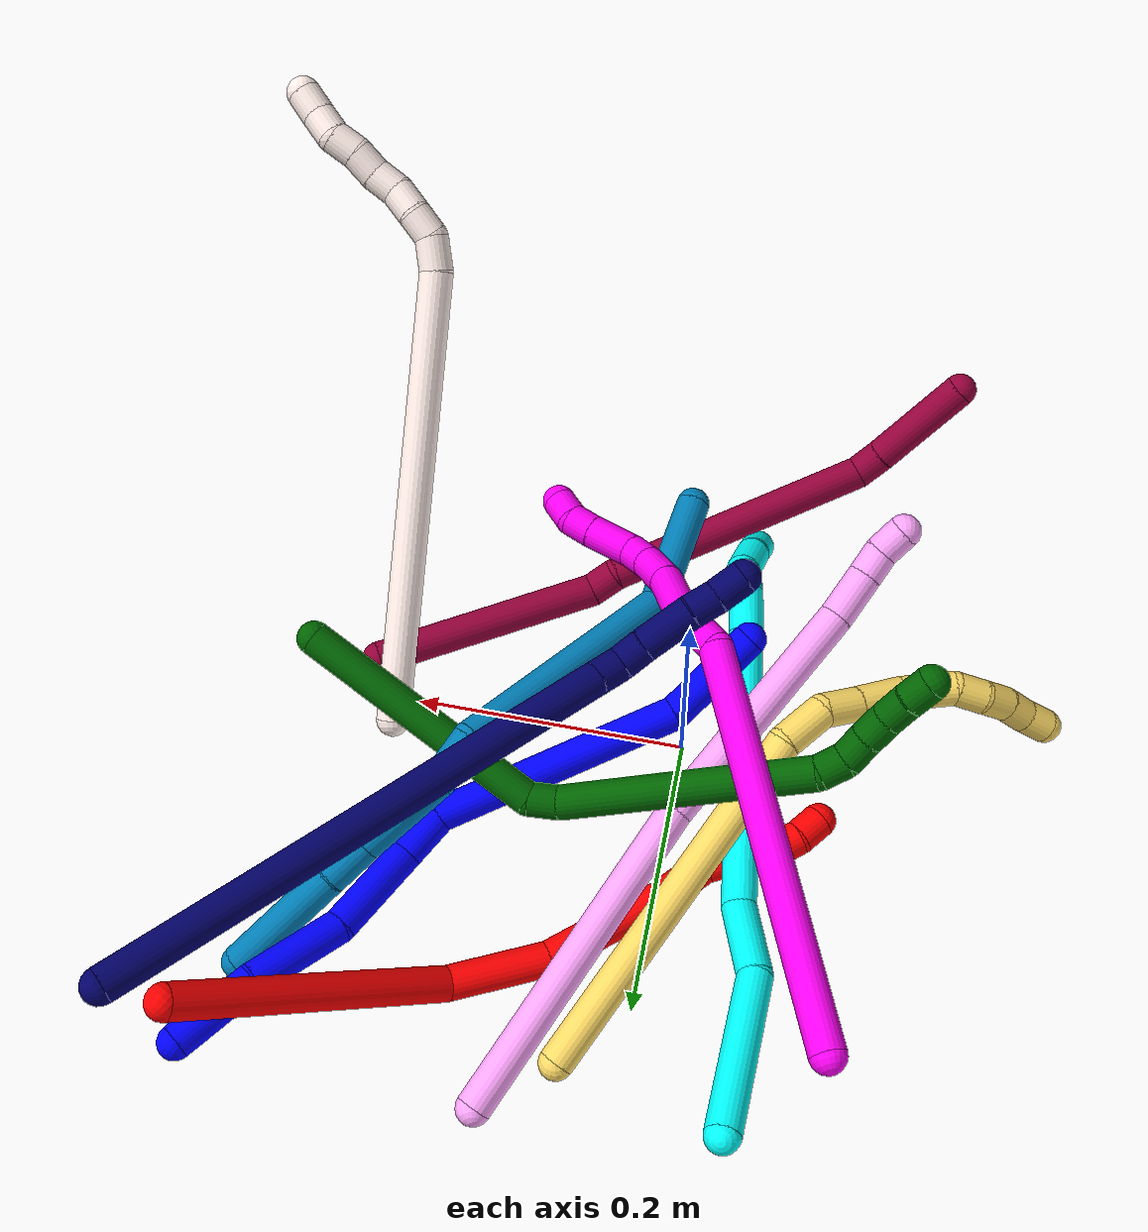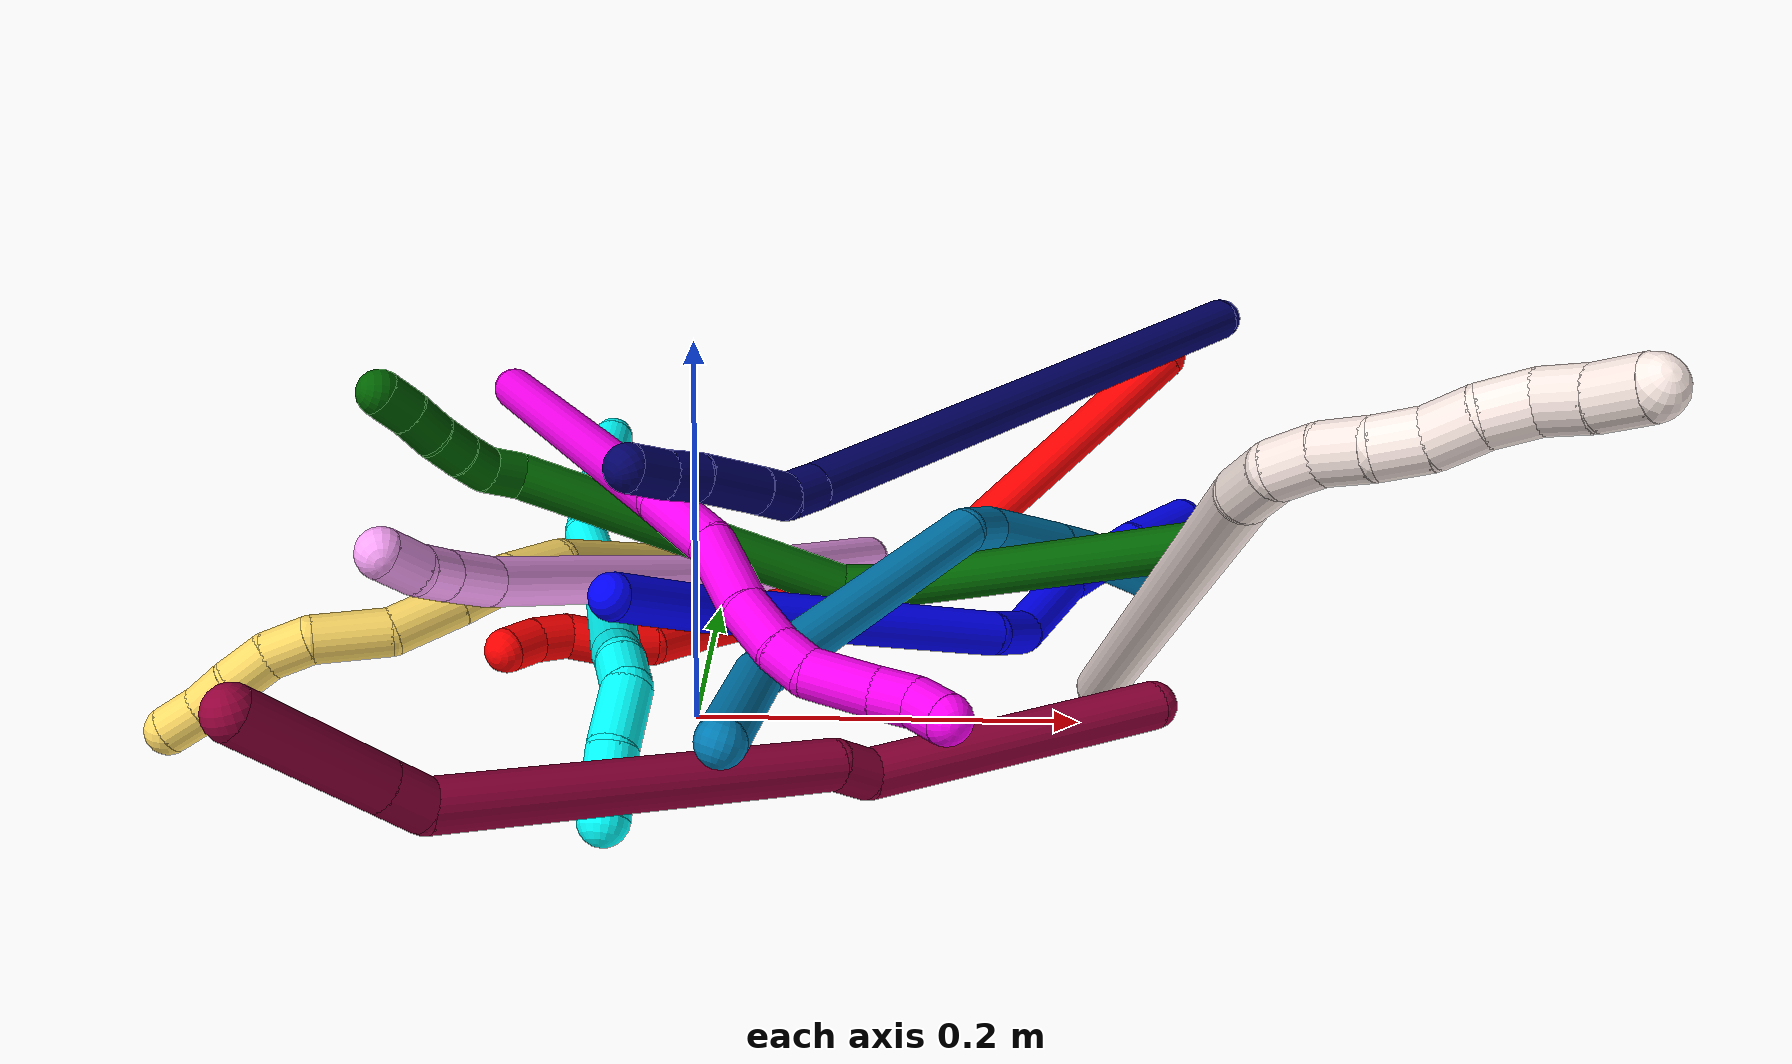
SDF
<sdf version="1.7">
 <world name="default">
  <plugin name="TubeGeneratorPlugin" filename="libtube_generator_plugin.so"/>
  <model name="photoneo_s_sensor">
   <static>1</static>
   <pose>0 0 2 1.57079 1.57079 3.14159</pose>
   <link name="link">
    <inertial><mass>0.1</mass></inertial>
    <sensor name="sensor" type="depth">
     <update_rate>30</update_rate>
     <camera>
      <horizontal_fov>1.22</horizontal_fov>
      <image><width>1920</width><height>1200</height><format>B8G8R8</format></image>
      <clip><near>0.1</near><far>4</far></clip>
      <depth_camera><output>points</output></depth_camera>
     </camera>
     <plugin name="camera_plugin" filename="libgazebo_ros_depth_camera.so">
      <baseline>0.2</baseline>
      <alwaysOn>1</alwaysOn>
      <updateRate>0.0</updateRate>
      <cameraName>camera_ir</cameraName>
      <imageTopicName>/camera/color/image_raw</imageTopicName>
      <cameraInfoTopicName>/camera/color/camera_info</cameraInfoTopicName>
      <depthImageTopicName>/camera/depth/image_raw</depthImageTopicName>
      <depthImageCameraInfoTopicName>/camera/depth/camera_info</depthImageCameraInfoTopicName>
      <pointCloudTopicName>/camera/depth/points</pointCloudTopicName>
      <frameName>fr_optical</frameName>
      <pointCloudCutoff>0.1</pointCloudCutoff>
      <pointCloudCutoffMax>2.0</pointCloudCutoffMax>
      <distortionK1>0</distortionK1>
      <distortionK2>0</distortionK2>
      <distortionK3>0</distortionK3>
      <distortionT1>0</distortionT1>
      <distortionT2>0</distortionT2>
      <CxPrime>0</CxPrime>
      <Cx>0</Cx>
      <Cy>0</Cy>
      <focalLength>0</focalLength>
      <hackBaseline>0</hackBaseline>
     </plugin>
    </sensor>
   </link>
  </model>
  <gravity>0 0 -9.8</gravity>
  <magnetic_field>6e-06 2.3e-05 -4.2e-05</magnetic_field>
  <atmosphere type="adiabatic"/>
  <physics name="default_physics" default="0" type="ode">
   <max_step_size>0.003</max_step_size>
   <real_time_factor>1</real_time_factor>
   <real_time_update_rate>1000</real_time_update_rate>
   <max_contacts>10000</max_contacts>
   <ode>
    <solver>
     <type>quick</type>
     <iters>100</iters>
     <sor>1.3</sor>
     <use_dynamic_moi_rescaling>0</use_dynamic_moi_rescaling>
    </solver>
    <constraints>
     <contact_max_correcting_vel>0</contact_max_correcting_vel>
     <contact_surface_layer>0.001</contact_surface_layer>
     <cfm>0</cfm>
     <erp>0.2</erp>
    </constraints>
   </ode>
  </physics>
  <scene><ambient>0.4 0.4 0.4 1</ambient><background>0.7 0.7 0.7 1</background><shadows>0</shadows></scene>
  <audio><device>default</device></audio>
  <spherical_coordinates>
   <surface_model>EARTH_WGS84</surface_model>
   <latitude_deg>0</latitude_deg>
   <longitude_deg>0</longitude_deg>
   <elevation>0</elevation>
   <heading_deg>0</heading_deg>
  </spherical_coordinates>
  <model name="bin">
   <static>1</static>
   <link name="bottom">
    <collision name="collision-bottom">
     <pose>0 0 -0.01 0 -0 0</pose>
     <geometry><box><size>0.8 0.6 0.02</size></box></geometry>
     <surface>
      <friction><ode><mu>100</mu><mu2>100</mu2></ode></friction>
      <contact><collide_bitmask>65535</collide_bitmask></contact>
     </surface>
    </collision>
   </link>
   <link name="west_wall">
    <collision name="collision-west_wall">
     <pose>-0.41 0 0.1 0 -0 0</pose>
     <geometry><box><size>0.02 0.6 0.2</size></box></geometry>
     <surface>
      <friction><ode><mu>100</mu><mu2>100</mu2></ode></friction>
      <contact><collide_bitmask>65535</collide_bitmask></contact>
     </surface>
    </collision>
   </link>
   <link name="east_wall">
    <collision name="collision-east_wall">
     <pose>0.41 0 0.1 0 -0 0</pose>
     <geometry><box><size>0.02 0.6 0.2</size></box></geometry>
     <surface>
      <friction><ode><mu>100</mu><mu2>100</mu2></ode></friction>
      <contact><collide_bitmask>65535</collide_bitmask></contact>
     </surface>
    </collision>
   </link>
   <link name="south_wall">
    <collision name="collision-south_wall">
     <pose>0 -0.31 0.1 0 -0 0</pose>
     <geometry><box><size>0.8 0.02 0.2</size></box></geometry>
     <surface>
      <friction><ode><mu>100</mu><mu2>100</mu2></ode></friction>
      <contact><collide_bitmask>65535</collide_bitmask></contact>
     </surface>
    </collision>
   </link>
   <link name="north_wall">
    <collision name="collision-north_wall">
     <pose>0 0.31 0.1 0 -0 0</pose>
     <geometry><box><size>0.8 0.02 0.2</size></box></geometry>
     <surface>
      <friction><ode><mu>100</mu><mu2>100</mu2></ode></friction>
      <contact><collide_bitmask>65535</collide_bitmask></contact>
     </surface>
    </collision>
   </link>
  </model>
  <model name="1">
   <static>0</static>
   <link name="1">
    <collision name="collision-cylinder-e_1_1_4">
     <pose>-0.01753 -0.010428 -0.023981 2.73139 -0.590569 -1.94192</pose>
     <geometry><cylinder><radius>0.0125</radius><length>0.062964</length></cylinder></geometry>
     <surface>
      <friction><ode><mu>1.16</mu><mu2>1.16</mu2><slip1>0</slip1><slip2>0</slip2></ode></friction>
      <contact><ode><kp>1e+06</kp><kd>1</kd><max_vel>0</max_vel><min_depth>0.001</min_depth></ode></contact>
     </surface>
    </collision>
    <visual name="visual-cylinder-e_1_1_4">
     <pose>-0.01753 -0.010428 -0.023981 2.73139 -0.590569 -1.94192</pose>
     <geometry><cylinder><radius>0.0125</radius><length>0.062964</length></cylinder></geometry>
     <material><ambient>0 0 1 1</ambient></material>
    </visual>
    <collision name="collision-cylinder-e_2_4_5">
     <pose>-0.056781 -0.036308 -0.070716 2.54508 -0.66841 -1.69224</pose>
     <geometry><cylinder><radius>0.0125</radius><length>0.070094</length></cylinder></geometry>
     <surface>
      <friction><ode><mu>1.16</mu><mu2>1.16</mu2><slip1>0</slip1><slip2>0</slip2></ode></friction>
      <contact><ode><kp>1e+06</kp><kd>1</kd><max_vel>0</max_vel><min_depth>0.001</min_depth></ode></contact>
     </surface>
    </collision>
    <visual name="visual-cylinder-e_2_4_5">
     <pose>-0.056781 -0.036308 -0.070716 2.54508 -0.66841 -1.69224</pose>
     <geometry><cylinder><radius>0.0125</radius><length>0.070094</length></cylinder></geometry>
     <material><ambient>0 0 1 1</ambient></material>
    </visual>
    <collision name="collision-cylinder-e_3_5_6">
     <pose>-0.103741 -0.058133 -0.11799 2.88727 -0.783548 -2.54136</pose>
     <geometry><cylinder><radius>0.0125</radius><length>0.071523</length></cylinder></geometry>
     <surface>
      <friction><ode><mu>1.16</mu><mu2>1.16</mu2><slip1>0</slip1><slip2>0</slip2></ode></friction>
      <contact><ode><kp>1e+06</kp><kd>1</kd><max_vel>0</max_vel><min_depth>0.001</min_depth></ode></contact>
     </surface>
    </collision>
    <visual name="visual-cylinder-e_3_5_6">
     <pose>-0.103741 -0.058133 -0.11799 2.88727 -0.783548 -2.54136</pose>
     <geometry><cylinder><radius>0.0125</radius><length>0.071523</length></cylinder></geometry>
     <material><ambient>0 0 1 1</ambient></material>
    </visual>
    <collision name="collision-cylinder-e_4_6_7">
     <pose>-0.135858 -0.067642 -0.159125 2.95512 -0.386246 -2.24954</pose>
     <geometry><cylinder><radius>0.0125</radius><length>0.036508</length></cylinder></geometry>
     <surface>
      <friction><ode><mu>1.16</mu><mu2>1.16</mu2><slip1>0</slip1><slip2>0</slip2></ode></friction>
      <contact><ode><kp>1e+06</kp><kd>1</kd><max_vel>0</max_vel><min_depth>0.001</min_depth></ode></contact>
     </surface>
    </collision>
    <visual name="visual-cylinder-e_4_6_7">
     <pose>-0.135858 -0.067642 -0.159125 2.95512 -0.386246 -2.24954</pose>
     <geometry><cylinder><radius>0.0125</radius><length>0.036508</length></cylinder></geometry>
     <material><ambient>0 0 1 1</ambient></material>
    </visual>
    <collision name="collision-cylinder-e_5_7_8">
     <pose>-0.15745 -0.121997 -0.250896 2.54337 -0.160408 -0.509958</pose>
     <geometry><cylinder><radius>0.0125</radius><length>0.184264</length></cylinder></geometry>
     <surface>
      <friction><ode><mu>1.16</mu><mu2>1.16</mu2><slip1>0</slip1><slip2>0</slip2></ode></friction>
      <contact><ode><kp>1e+06</kp><kd>1</kd><max_vel>0</max_vel><min_depth>0.001</min_depth></ode></contact>
     </surface>
    </collision>
    <visual name="visual-cylinder-e_5_7_8">
     <pose>-0.15745 -0.121997 -0.250896 2.54337 -0.160408 -0.509958</pose>
     <geometry><cylinder><radius>0.0125</radius><length>0.184264</length></cylinder></geometry>
     <material><ambient>0 0 1 1</ambient></material>
    </visual>
    <collision name="collision-cylinder-e_6_8_2">
     <pose>-0.182238 -0.181707 -0.360972 2.90313 -0.273255 -1.70803</pose>
     <geometry><cylinder><radius>0.0125</radius><length>0.074647</length></cylinder></geometry>
     <surface>
      <friction><ode><mu>1.16</mu><mu2>1.16</mu2><slip1>0</slip1><slip2>0</slip2></ode></friction>
      <contact><ode><kp>1e+06</kp><kd>1</kd><max_vel>0</max_vel><min_depth>0.001</min_depth></ode></contact>
     </surface>
    </collision>
    <visual name="visual-cylinder-e_6_8_2">
     <pose>-0.182238 -0.181707 -0.360972 2.90313 -0.273255 -1.70803</pose>
     <geometry><cylinder><radius>0.0125</radius><length>0.074647</length></cylinder></geometry>
     <material><ambient>0 0 1 1</ambient></material>
    </visual>
    <collision name="collision-sphere-2">
     <pose>-0.19231 -0.190196 -0.395893 0 -0 0</pose>
     <geometry><sphere><radius>0.0125</radius></sphere></geometry>
     <surface>
      <friction><ode><mu>1.16</mu><mu2>1.16</mu2><slip1>0</slip1><slip2>0</slip2></ode></friction>
      <contact><ode><kp>1e+06</kp><kd>1</kd><max_vel>0</max_vel><min_depth>0.001</min_depth></ode></contact>
     </surface>
    </collision>
    <visual name="visual-sphere-2">
     <pose>-0.19231 -0.190196 -0.395893 0 -0 0</pose>
     <geometry><sphere><radius>0.0125</radius></sphere></geometry>
     <material><ambient>0 0 1 1</ambient></material>
    </visual>
    <collision name="collision-sphere-4">
     <pose>-0.035061 -0.020857 -0.047961 0 -0 0</pose>
     <geometry><sphere><radius>0.0125</radius></sphere></geometry>
     <surface>
      <friction><ode><mu>1.16</mu><mu2>1.16</mu2><slip1>0</slip1><slip2>0</slip2></ode></friction>
      <contact><ode><kp>1e+06</kp><kd>1</kd><max_vel>0</max_vel><min_depth>0.001</min_depth></ode></contact>
     </surface>
    </collision>
    <visual name="visual-sphere-4">
     <pose>-0.035061 -0.020857 -0.047961 0 -0 0</pose>
     <geometry><sphere><radius>0.0125</radius></sphere></geometry>
     <material><ambient>0 0 1 1</ambient></material>
    </visual>
    <collision name="collision-sphere-1">
     <geometry><sphere><radius>0.0125</radius></sphere></geometry>
     <surface>
      <friction><ode><mu>1.16</mu><mu2>1.16</mu2><slip1>0</slip1><slip2>0</slip2></ode></friction>
      <contact><ode><kp>1e+06</kp><kd>1</kd><max_vel>0</max_vel><min_depth>0.001</min_depth></ode></contact>
     </surface>
    </collision>
    <visual name="visual-sphere-1">
     <geometry><sphere><radius>0.0125</radius></sphere></geometry>
     <material><ambient>0 0 1 1</ambient></material>
    </visual>
    <collision name="collision-sphere-8">
     <pose>-0.172165 -0.173218 -0.32605 0 -0 0</pose>
     <geometry><sphere><radius>0.0125</radius></sphere></geometry>
     <surface>
      <friction><ode><mu>1.16</mu><mu2>1.16</mu2><slip1>0</slip1><slip2>0</slip2></ode></friction>
      <contact><ode><kp>1e+06</kp><kd>1</kd><max_vel>0</max_vel><min_depth>0.001</min_depth></ode></contact>
     </surface>
    </collision>
    <visual name="visual-sphere-8">
     <pose>-0.172165 -0.173218 -0.32605 0 -0 0</pose>
     <geometry><sphere><radius>0.0125</radius></sphere></geometry>
     <material><ambient>0 0 1 1</ambient></material>
    </visual>
    <collision name="collision-sphere-5">
     <pose>-0.078501 -0.051759 -0.093471 0 -0 0</pose>
     <geometry><sphere><radius>0.0125</radius></sphere></geometry>
     <surface>
      <friction><ode><mu>1.16</mu><mu2>1.16</mu2><slip1>0</slip1><slip2>0</slip2></ode></friction>
      <contact><ode><kp>1e+06</kp><kd>1</kd><max_vel>0</max_vel><min_depth>0.001</min_depth></ode></contact>
     </surface>
    </collision>
    <visual name="visual-sphere-5">
     <pose>-0.078501 -0.051759 -0.093471 0 -0 0</pose>
     <geometry><sphere><radius>0.0125</radius></sphere></geometry>
     <material><ambient>0 0 1 1</ambient></material>
    </visual>
    <collision name="collision-sphere-6">
     <pose>-0.128981 -0.064507 -0.142509 0 -0 0</pose>
     <geometry><sphere><radius>0.0125</radius></sphere></geometry>
     <surface>
      <friction><ode><mu>1.16</mu><mu2>1.16</mu2><slip1>0</slip1><slip2>0</slip2></ode></friction>
      <contact><ode><kp>1e+06</kp><kd>1</kd><max_vel>0</max_vel><min_depth>0.001</min_depth></ode></contact>
     </surface>
    </collision>
    <visual name="visual-sphere-6">
     <pose>-0.128981 -0.064507 -0.142509 0 -0 0</pose>
     <geometry><sphere><radius>0.0125</radius></sphere></geometry>
     <material><ambient>0 0 1 1</ambient></material>
    </visual>
    <collision name="collision-sphere-7">
     <pose>-0.142735 -0.070777 -0.175741 0 -0 0</pose>
     <geometry><sphere><radius>0.0125</radius></sphere></geometry>
     <surface>
      <friction><ode><mu>1.16</mu><mu2>1.16</mu2><slip1>0</slip1><slip2>0</slip2></ode></friction>
      <contact><ode><kp>1e+06</kp><kd>1</kd><max_vel>0</max_vel><min_depth>0.001</min_depth></ode></contact>
     </surface>
    </collision>
    <visual name="visual-sphere-7">
     <pose>-0.142735 -0.070777 -0.175741 0 -0 0</pose>
     <geometry><sphere><radius>0.0125</radius></sphere></geometry>
     <material><ambient>0 0 1 1</ambient></material>
    </visual>
    <inertial>
     <pose>-0.120159 -0.091745 -0.187783 0 -0 0</pose>
     <mass>0.5</mass>
     <inertia>
      <ixx>5.2e-05</ixx>
      <ixy>0</ixy>
      <ixz>0</ixz>
      <iyy>-0.000656</iyy>
      <iyz>0</iyz>
      <izz>0.000452</izz>
     </inertia>
    </inertial>
   </link>
   <pose>0.292399 0.287967 0.03885 2.6935 -0.829293 1.6114</pose>
  </model>
  <model name="2">
   <static>0</static>
   <link name="2">
    <collision name="collision-cylinder-e_1_1_4">
     <pose>-0.071436 0.027674 -0.069309 -2.7617 -0.763537 2.24834</pose>
     <geometry><cylinder><radius>0.0125</radius><length>0.206617</length></cylinder></geometry>
     <surface>
      <friction><ode><mu>1.16</mu><mu2>1.16</mu2><slip1>0</slip1><slip2>0</slip2></ode></friction>
      <contact><ode><kp>1e+06</kp><kd>1</kd><max_vel>0</max_vel><min_depth>0.001</min_depth></ode></contact>
     </surface>
    </collision>
    <visual name="visual-cylinder-e_1_1_4">
     <pose>-0.071436 0.027674 -0.069309 -2.7617 -0.763537 2.24834</pose>
     <geometry><cylinder><radius>0.0125</radius><length>0.206617</length></cylinder></geometry>
     <material><ambient>1 0 0 1</ambient></material>
    </visual>
    <collision name="collision-cylinder-e_2_4_5">
     <pose>-0.164244 0.047583 -0.166963 2.87423 -0.628759 -2.35725</pose>
     <geometry><cylinder><radius>0.0125</radius><length>0.072677</length></cylinder></geometry>
     <surface>
      <friction><ode><mu>1.16</mu><mu2>1.16</mu2><slip1>0</slip1><slip2>0</slip2></ode></friction>
      <contact><ode><kp>1e+06</kp><kd>1</kd><max_vel>0</max_vel><min_depth>0.001</min_depth></ode></contact>
     </surface>
    </collision>
    <visual name="visual-cylinder-e_2_4_5">
     <pose>-0.164244 0.047583 -0.166963 2.87423 -0.628759 -2.35725</pose>
     <geometry><cylinder><radius>0.0125</radius><length>0.072677</length></cylinder></geometry>
     <material><ambient>1 0 0 1</ambient></material>
    </visual>
    <collision name="collision-cylinder-e_3_5_6">
     <pose>-0.202391 0.029498 -0.236348 2.89522 -0.3774 -1.99119</pose>
     <geometry><cylinder><radius>0.0125</radius><length>0.091043</length></cylinder></geometry>
     <surface>
      <friction><ode><mu>1.16</mu><mu2>1.16</mu2><slip1>0</slip1><slip2>0</slip2></ode></friction>
      <contact><ode><kp>1e+06</kp><kd>1</kd><max_vel>0</max_vel><min_depth>0.001</min_depth></ode></contact>
     </surface>
    </collision>
    <visual name="visual-cylinder-e_3_5_6">
     <pose>-0.202391 0.029498 -0.236348 2.89522 -0.3774 -1.99119</pose>
     <geometry><cylinder><radius>0.0125</radius><length>0.091043</length></cylinder></geometry>
     <material><ambient>1 0 0 1</ambient></material>
    </visual>
    <collision name="collision-cylinder-e_4_6_7">
     <pose>-0.223803 0.015345 -0.295407 2.93201 -0.246578 -1.73404</pose>
     <geometry><cylinder><radius>0.0125</radius><length>0.037995</length></cylinder></geometry>
     <surface>
      <friction><ode><mu>1.16</mu><mu2>1.16</mu2><slip1>0</slip1><slip2>0</slip2></ode></friction>
      <contact><ode><kp>1e+06</kp><kd>1</kd><max_vel>0</max_vel><min_depth>0.001</min_depth></ode></contact>
     </surface>
    </collision>
    <visual name="visual-cylinder-e_4_6_7">
     <pose>-0.223803 0.015345 -0.295407 2.93201 -0.246578 -1.73404</pose>
     <geometry><cylinder><radius>0.0125</radius><length>0.037995</length></cylinder></geometry>
     <material><ambient>1 0 0 1</ambient></material>
    </visual>
    <collision name="collision-cylinder-e_5_7_8">
     <pose>-0.234981 0.005953 -0.323092 2.61964 -0.530589 -1.58798</pose>
     <geometry><cylinder><radius>0.0125</radius><length>0.025854</length></cylinder></geometry>
     <surface>
      <friction><ode><mu>1.16</mu><mu2>1.16</mu2><slip1>0</slip1><slip2>0</slip2></ode></friction>
      <contact><ode><kp>1e+06</kp><kd>1</kd><max_vel>0</max_vel><min_depth>0.001</min_depth></ode></contact>
     </surface>
    </collision>
    <visual name="visual-cylinder-e_5_7_8">
     <pose>-0.234981 0.005953 -0.323092 2.61964 -0.530589 -1.58798</pose>
     <geometry><cylinder><radius>0.0125</radius><length>0.025854</length></cylinder></geometry>
     <material><ambient>1 0 0 1</ambient></material>
    </visual>
    <collision name="collision-cylinder-e_6_8_9">
     <pose>-0.248394 -0.006854 -0.339927 2.35084 -0.592993 -1.26376</pose>
     <geometry><cylinder><radius>0.0125</radius><length>0.024589</length></cylinder></geometry>
     <surface>
      <friction><ode><mu>1.16</mu><mu2>1.16</mu2><slip1>0</slip1><slip2>0</slip2></ode></friction>
      <contact><ode><kp>1e+06</kp><kd>1</kd><max_vel>0</max_vel><min_depth>0.001</min_depth></ode></contact>
     </surface>
    </collision>
    <visual name="visual-cylinder-e_6_8_9">
     <pose>-0.248394 -0.006854 -0.339927 2.35084 -0.592993 -1.26376</pose>
     <geometry><cylinder><radius>0.0125</radius><length>0.024589</length></cylinder></geometry>
     <material><ambient>1 0 0 1</ambient></material>
    </visual>
    <collision name="collision-cylinder-e_7_9_10">
     <pose>-0.259075 -0.01737 -0.35632 2.80098 -0.371382 -1.65903</pose>
     <geometry><cylinder><radius>0.0125</radius><length>0.021</length></cylinder></geometry>
     <surface>
      <friction><ode><mu>1.16</mu><mu2>1.16</mu2><slip1>0</slip1><slip2>0</slip2></ode></friction>
      <contact><ode><kp>1e+06</kp><kd>1</kd><max_vel>0</max_vel><min_depth>0.001</min_depth></ode></contact>
     </surface>
    </collision>
    <visual name="visual-cylinder-e_7_9_10">
     <pose>-0.259075 -0.01737 -0.35632 2.80098 -0.371382 -1.65903</pose>
     <geometry><cylinder><radius>0.0125</radius><length>0.021</length></cylinder></geometry>
     <material><ambient>1 0 0 1</ambient></material>
    </visual>
    <collision name="collision-cylinder-e_8_10_2">
     <pose>-0.264946 -0.022027 -0.375345 3.00091 -0.205152 -1.94111</pose>
     <geometry><cylinder><radius>0.0125</radius><length>0.020226</length></cylinder></geometry>
     <surface>
      <friction><ode><mu>1.16</mu><mu2>1.16</mu2><slip1>0</slip1><slip2>0</slip2></ode></friction>
      <contact><ode><kp>1e+06</kp><kd>1</kd><max_vel>0</max_vel><min_depth>0.001</min_depth></ode></contact>
     </surface>
    </collision>
    <visual name="visual-cylinder-e_8_10_2">
     <pose>-0.264946 -0.022027 -0.375345 3.00091 -0.205152 -1.94111</pose>
     <geometry><cylinder><radius>0.0125</radius><length>0.020226</length></cylinder></geometry>
     <material><ambient>1 0 0 1</ambient></material>
    </visual>
    <collision name="collision-sphere-2">
     <pose>-0.267006 -0.023415 -0.385148 0 -0 0</pose>
     <geometry><sphere><radius>0.0125</radius></sphere></geometry>
     <surface>
      <friction><ode><mu>1.16</mu><mu2>1.16</mu2><slip1>0</slip1><slip2>0</slip2></ode></friction>
      <contact><ode><kp>1e+06</kp><kd>1</kd><max_vel>0</max_vel><min_depth>0.001</min_depth></ode></contact>
     </surface>
    </collision>
    <visual name="visual-sphere-2">
     <pose>-0.267006 -0.023415 -0.385148 0 -0 0</pose>
     <geometry><sphere><radius>0.0125</radius></sphere></geometry>
     <material><ambient>1 0 0 1</ambient></material>
    </visual>
    <collision name="collision-sphere-10">
     <pose>-0.262885 -0.020639 -0.365542 0 -0 0</pose>
     <geometry><sphere><radius>0.0125</radius></sphere></geometry>
     <surface>
      <friction><ode><mu>1.16</mu><mu2>1.16</mu2><slip1>0</slip1><slip2>0</slip2></ode></friction>
      <contact><ode><kp>1e+06</kp><kd>1</kd><max_vel>0</max_vel><min_depth>0.001</min_depth></ode></contact>
     </surface>
    </collision>
    <visual name="visual-sphere-10">
     <pose>-0.262885 -0.020639 -0.365542 0 -0 0</pose>
     <geometry><sphere><radius>0.0125</radius></sphere></geometry>
     <material><ambient>1 0 0 1</ambient></material>
    </visual>
    <collision name="collision-sphere-9">
     <pose>-0.255264 -0.014102 -0.347098 0 -0 0</pose>
     <geometry><sphere><radius>0.0125</radius></sphere></geometry>
     <surface>
      <friction><ode><mu>1.16</mu><mu2>1.16</mu2><slip1>0</slip1><slip2>0</slip2></ode></friction>
      <contact><ode><kp>1e+06</kp><kd>1</kd><max_vel>0</max_vel><min_depth>0.001</min_depth></ode></contact>
     </surface>
    </collision>
    <visual name="visual-sphere-9">
     <pose>-0.255264 -0.014102 -0.347098 0 -0 0</pose>
     <geometry><sphere><radius>0.0125</radius></sphere></geometry>
     <material><ambient>1 0 0 1</ambient></material>
    </visual>
    <collision name="collision-sphere-4">
     <pose>-0.142872 0.055348 -0.138618 0 -0 0</pose>
     <geometry><sphere><radius>0.0125</radius></sphere></geometry>
     <surface>
      <friction><ode><mu>1.16</mu><mu2>1.16</mu2><slip1>0</slip1><slip2>0</slip2></ode></friction>
      <contact><ode><kp>1e+06</kp><kd>1</kd><max_vel>0</max_vel><min_depth>0.001</min_depth></ode></contact>
     </surface>
    </collision>
    <visual name="visual-sphere-4">
     <pose>-0.142872 0.055348 -0.138618 0 -0 0</pose>
     <geometry><sphere><radius>0.0125</radius></sphere></geometry>
     <material><ambient>1 0 0 1</ambient></material>
    </visual>
    <collision name="collision-sphere-1">
     <geometry><sphere><radius>0.0125</radius></sphere></geometry>
     <surface>
      <friction><ode><mu>1.16</mu><mu2>1.16</mu2><slip1>0</slip1><slip2>0</slip2></ode></friction>
      <contact><ode><kp>1e+06</kp><kd>1</kd><max_vel>0</max_vel><min_depth>0.001</min_depth></ode></contact>
     </surface>
    </collision>
    <visual name="visual-sphere-1">
     <geometry><sphere><radius>0.0125</radius></sphere></geometry>
     <material><ambient>1 0 0 1</ambient></material>
    </visual>
    <collision name="collision-sphere-8">
     <pose>-0.241523 0.000394 -0.332757 0 -0 0</pose>
     <geometry><sphere><radius>0.0125</radius></sphere></geometry>
     <surface>
      <friction><ode><mu>1.16</mu><mu2>1.16</mu2><slip1>0</slip1><slip2>0</slip2></ode></friction>
      <contact><ode><kp>1e+06</kp><kd>1</kd><max_vel>0</max_vel><min_depth>0.001</min_depth></ode></contact>
     </surface>
    </collision>
    <visual name="visual-sphere-8">
     <pose>-0.241523 0.000394 -0.332757 0 -0 0</pose>
     <geometry><sphere><radius>0.0125</radius></sphere></geometry>
     <material><ambient>1 0 0 1</ambient></material>
    </visual>
    <collision name="collision-sphere-5">
     <pose>-0.185616 0.039819 -0.195308 0 -0 0</pose>
     <geometry><sphere><radius>0.0125</radius></sphere></geometry>
     <surface>
      <friction><ode><mu>1.16</mu><mu2>1.16</mu2><slip1>0</slip1><slip2>0</slip2></ode></friction>
      <contact><ode><kp>1e+06</kp><kd>1</kd><max_vel>0</max_vel><min_depth>0.001</min_depth></ode></contact>
     </surface>
    </collision>
    <visual name="visual-sphere-5">
     <pose>-0.185616 0.039819 -0.195308 0 -0 0</pose>
     <geometry><sphere><radius>0.0125</radius></sphere></geometry>
     <material><ambient>1 0 0 1</ambient></material>
    </visual>
    <collision name="collision-sphere-6">
     <pose>-0.219166 0.019178 -0.277388 0 -0 0</pose>
     <geometry><sphere><radius>0.0125</radius></sphere></geometry>
     <surface>
      <friction><ode><mu>1.16</mu><mu2>1.16</mu2><slip1>0</slip1><slip2>0</slip2></ode></friction>
      <contact><ode><kp>1e+06</kp><kd>1</kd><max_vel>0</max_vel><min_depth>0.001</min_depth></ode></contact>
     </surface>
    </collision>
    <visual name="visual-sphere-6">
     <pose>-0.219166 0.019178 -0.277388 0 -0 0</pose>
     <geometry><sphere><radius>0.0125</radius></sphere></geometry>
     <material><ambient>1 0 0 1</ambient></material>
    </visual>
    <collision name="collision-sphere-7">
     <pose>-0.22844 0.011512 -0.313427 0 -0 0</pose>
     <geometry><sphere><radius>0.0125</radius></sphere></geometry>
     <surface>
      <friction><ode><mu>1.16</mu><mu2>1.16</mu2><slip1>0</slip1><slip2>0</slip2></ode></friction>
      <contact><ode><kp>1e+06</kp><kd>1</kd><max_vel>0</max_vel><min_depth>0.001</min_depth></ode></contact>
     </surface>
    </collision>
    <visual name="visual-sphere-7">
     <pose>-0.22844 0.011512 -0.313427 0 -0 0</pose>
     <geometry><sphere><radius>0.0125</radius></sphere></geometry>
     <material><ambient>1 0 0 1</ambient></material>
    </visual>
    <inertial>
     <pose>-0.153217 0.02324 -0.181965 0 -0 0</pose>
     <mass>0.5</mass>
     <inertia>
      <ixx>-7.4e-05</ixx>
      <ixy>0</ixy>
      <ixz>0</ixz>
      <iyy>0.000971</iyy>
      <iyz>0</iyz>
      <izz>0.000361</izz>
     </inertia>
    </inertial>
   </link>
   <pose>0.27662 0.28561 0.143308 -1.4806 -0.432116 -0.45858</pose>
  </model>
  <model name="3">
   <static>0</static>
   <link name="3">
    <collision name="collision-cylinder-e_1_1_4">
     <pose>-0.000937 -0.038021 -0.045447 2.44493 -0.015808 -0.043526</pose>
     <geometry><cylinder><radius>0.0125</radius><length>0.118523</length></cylinder></geometry>
     <surface>
      <friction><ode><mu>1.16</mu><mu2>1.16</mu2><slip1>0</slip1><slip2>0</slip2></ode></friction>
      <contact><ode><kp>1e+06</kp><kd>1</kd><max_vel>0</max_vel><min_depth>0.001</min_depth></ode></contact>
     </surface>
    </collision>
    <visual name="visual-cylinder-e_1_1_4">
     <pose>-0.000937 -0.038021 -0.045447 2.44493 -0.015808 -0.043526</pose>
     <geometry><cylinder><radius>0.0125</radius><length>0.118523</length></cylinder></geometry>
     <material><ambient>0.003922 1 0.996078 1</ambient></material>
    </visual>
    <collision name="collision-cylinder-e_2_4_5">
     <pose>0.008036 -0.092877 -0.112702 2.48419 0.345266 0.945183</pose>
     <geometry><cylinder><radius>0.0125</radius><length>0.058556</length></cylinder></geometry>
     <surface>
      <friction><ode><mu>1.16</mu><mu2>1.16</mu2><slip1>0</slip1><slip2>0</slip2></ode></friction>
      <contact><ode><kp>1e+06</kp><kd>1</kd><max_vel>0</max_vel><min_depth>0.001</min_depth></ode></contact>
     </surface>
    </collision>
    <visual name="visual-cylinder-e_2_4_5">
     <pose>0.008036 -0.092877 -0.112702 2.48419 0.345266 0.945183</pose>
     <geometry><cylinder><radius>0.0125</radius><length>0.058556</length></cylinder></geometry>
     <material><ambient>0.003922 1 0.996078 1</ambient></material>
    </visual>
    <collision name="collision-cylinder-e_3_5_6">
     <pose>0.030408 -0.200261 -0.176961 2.00918 0.12399 0.194699</pose>
     <geometry><cylinder><radius>0.0125</radius><length>0.201559</length></cylinder></geometry>
     <surface>
      <friction><ode><mu>1.16</mu><mu2>1.16</mu2><slip1>0</slip1><slip2>0</slip2></ode></friction>
      <contact><ode><kp>1e+06</kp><kd>1</kd><max_vel>0</max_vel><min_depth>0.001</min_depth></ode></contact>
     </surface>
    </collision>
    <visual name="visual-cylinder-e_3_5_6">
     <pose>0.030408 -0.200261 -0.176961 2.00918 0.12399 0.194699</pose>
     <geometry><cylinder><radius>0.0125</radius><length>0.201559</length></cylinder></geometry>
     <material><ambient>0.003922 1 0.996078 1</ambient></material>
    </visual>
    <collision name="collision-cylinder-e_4_6_7">
     <pose>0.045334 -0.305627 -0.225452 1.95795 0.15269 0.226617</pose>
     <geometry><cylinder><radius>0.0125</radius><length>0.032379</length></cylinder></geometry>
     <surface>
      <friction><ode><mu>1.16</mu><mu2>1.16</mu2><slip1>0</slip1><slip2>0</slip2></ode></friction>
      <contact><ode><kp>1e+06</kp><kd>1</kd><max_vel>0</max_vel><min_depth>0.001</min_depth></ode></contact>
     </surface>
    </collision>
    <visual name="visual-cylinder-e_4_6_7">
     <pose>0.045334 -0.305627 -0.225452 1.95795 0.15269 0.226617</pose>
     <geometry><cylinder><radius>0.0125</radius><length>0.032379</length></cylinder></geometry>
     <material><ambient>0.003922 1 0.996078 1</ambient></material>
    </visual>
    <collision name="collision-cylinder-e_5_7_8">
     <pose>0.050495 -0.327089 -0.239216 2.43105 0.258946 0.675014</pose>
     <geometry><cylinder><radius>0.0125</radius><length>0.021079</length></cylinder></geometry>
     <surface>
      <friction><ode><mu>1.16</mu><mu2>1.16</mu2><slip1>0</slip1><slip2>0</slip2></ode></friction>
      <contact><ode><kp>1e+06</kp><kd>1</kd><max_vel>0</max_vel><min_depth>0.001</min_depth></ode></contact>
     </surface>
    </collision>
    <visual name="visual-cylinder-e_5_7_8">
     <pose>0.050495 -0.327089 -0.239216 2.43105 0.258946 0.675014</pose>
     <geometry><cylinder><radius>0.0125</radius><length>0.021079</length></cylinder></geometry>
     <material><ambient>0.003922 1 0.996078 1</ambient></material>
    </visual>
    <collision name="collision-cylinder-e_6_8_9">
     <pose>0.052001 -0.33937 -0.262785 2.79987 -0.070797 -0.404866</pose>
     <geometry><cylinder><radius>0.0125</radius><length>0.033722</length></cylinder></geometry>
     <surface>
      <friction><ode><mu>1.16</mu><mu2>1.16</mu2><slip1>0</slip1><slip2>0</slip2></ode></friction>
      <contact><ode><kp>1e+06</kp><kd>1</kd><max_vel>0</max_vel><min_depth>0.001</min_depth></ode></contact>
     </surface>
    </collision>
    <visual name="visual-cylinder-e_6_8_9">
     <pose>0.052001 -0.33937 -0.262785 2.79987 -0.070797 -0.404866</pose>
     <geometry><cylinder><radius>0.0125</radius><length>0.033722</length></cylinder></geometry>
     <material><ambient>0.003922 1 0.996078 1</ambient></material>
    </visual>
    <collision name="collision-cylinder-e_7_9_2">
     <pose>0.050962 -0.346876 -0.29562 3.032 0.00895 0.1628</pose>
     <geometry><cylinder><radius>0.0125</radius><length>0.034182</length></cylinder></geometry>
     <surface>
      <friction><ode><mu>1.16</mu><mu2>1.16</mu2><slip1>0</slip1><slip2>0</slip2></ode></friction>
      <contact><ode><kp>1e+06</kp><kd>1</kd><max_vel>0</max_vel><min_depth>0.001</min_depth></ode></contact>
     </surface>
    </collision>
    <visual name="visual-cylinder-e_7_9_2">
     <pose>0.050962 -0.346876 -0.29562 3.032 0.00895 0.1628</pose>
     <geometry><cylinder><radius>0.0125</radius><length>0.034182</length></cylinder></geometry>
     <material><ambient>0.003922 1 0.996078 1</ambient></material>
    </visual>
    <collision name="collision-sphere-2">
     <pose>0.051115 -0.348745 -0.312607 0 -0 0</pose>
     <geometry><sphere><radius>0.0125</radius></sphere></geometry>
     <surface>
      <friction><ode><mu>1.16</mu><mu2>1.16</mu2><slip1>0</slip1><slip2>0</slip2></ode></friction>
      <contact><ode><kp>1e+06</kp><kd>1</kd><max_vel>0</max_vel><min_depth>0.001</min_depth></ode></contact>
     </surface>
    </collision>
    <visual name="visual-sphere-2">
     <pose>0.051115 -0.348745 -0.312607 0 -0 0</pose>
     <geometry><sphere><radius>0.0125</radius></sphere></geometry>
     <material><ambient>0.003922 1 0.996078 1</ambient></material>
    </visual>
    <collision name="collision-sphere-9">
     <pose>0.050809 -0.345007 -0.278632 0 -0 0</pose>
     <geometry><sphere><radius>0.0125</radius></sphere></geometry>
     <surface>
      <friction><ode><mu>1.16</mu><mu2>1.16</mu2><slip1>0</slip1><slip2>0</slip2></ode></friction>
      <contact><ode><kp>1e+06</kp><kd>1</kd><max_vel>0</max_vel><min_depth>0.001</min_depth></ode></contact>
     </surface>
    </collision>
    <visual name="visual-sphere-9">
     <pose>0.050809 -0.345007 -0.278632 0 -0 0</pose>
     <geometry><sphere><radius>0.0125</radius></sphere></geometry>
     <material><ambient>0.003922 1 0.996078 1</ambient></material>
    </visual>
    <collision name="collision-sphere-4">
     <pose>-0.001874 -0.076042 -0.090894 0 -0 0</pose>
     <geometry><sphere><radius>0.0125</radius></sphere></geometry>
     <surface>
      <friction><ode><mu>1.16</mu><mu2>1.16</mu2><slip1>0</slip1><slip2>0</slip2></ode></friction>
      <contact><ode><kp>1e+06</kp><kd>1</kd><max_vel>0</max_vel><min_depth>0.001</min_depth></ode></contact>
     </surface>
    </collision>
    <visual name="visual-sphere-4">
     <pose>-0.001874 -0.076042 -0.090894 0 -0 0</pose>
     <geometry><sphere><radius>0.0125</radius></sphere></geometry>
     <material><ambient>0.003922 1 0.996078 1</ambient></material>
    </visual>
    <collision name="collision-sphere-1">
     <geometry><sphere><radius>0.0125</radius></sphere></geometry>
     <surface>
      <friction><ode><mu>1.16</mu><mu2>1.16</mu2><slip1>0</slip1><slip2>0</slip2></ode></friction>
      <contact><ode><kp>1e+06</kp><kd>1</kd><max_vel>0</max_vel><min_depth>0.001</min_depth></ode></contact>
     </surface>
    </collision>
    <visual name="visual-sphere-1">
     <geometry><sphere><radius>0.0125</radius></sphere></geometry>
     <material><ambient>0.003922 1 0.996078 1</ambient></material>
    </visual>
    <collision name="collision-sphere-8">
     <pose>0.053194 -0.333734 -0.246939 0 -0 0</pose>
     <geometry><sphere><radius>0.0125</radius></sphere></geometry>
     <surface>
      <friction><ode><mu>1.16</mu><mu2>1.16</mu2><slip1>0</slip1><slip2>0</slip2></ode></friction>
      <contact><ode><kp>1e+06</kp><kd>1</kd><max_vel>0</max_vel><min_depth>0.001</min_depth></ode></contact>
     </surface>
    </collision>
    <visual name="visual-sphere-8">
     <pose>0.053194 -0.333734 -0.246939 0 -0 0</pose>
     <geometry><sphere><radius>0.0125</radius></sphere></geometry>
     <material><ambient>0.003922 1 0.996078 1</ambient></material>
    </visual>
    <collision name="collision-sphere-5">
     <pose>0.017945 -0.109712 -0.13451 0 -0 0</pose>
     <geometry><sphere><radius>0.0125</radius></sphere></geometry>
     <surface>
      <friction><ode><mu>1.16</mu><mu2>1.16</mu2><slip1>0</slip1><slip2>0</slip2></ode></friction>
      <contact><ode><kp>1e+06</kp><kd>1</kd><max_vel>0</max_vel><min_depth>0.001</min_depth></ode></contact>
     </surface>
    </collision>
    <visual name="visual-sphere-5">
     <pose>0.017945 -0.109712 -0.13451 0 -0 0</pose>
     <geometry><sphere><radius>0.0125</radius></sphere></geometry>
     <material><ambient>0.003922 1 0.996078 1</ambient></material>
    </visual>
    <collision name="collision-sphere-6">
     <pose>0.042872 -0.29081 -0.219411 0 -0 0</pose>
     <geometry><sphere><radius>0.0125</radius></sphere></geometry>
     <surface>
      <friction><ode><mu>1.16</mu><mu2>1.16</mu2><slip1>0</slip1><slip2>0</slip2></ode></friction>
      <contact><ode><kp>1e+06</kp><kd>1</kd><max_vel>0</max_vel><min_depth>0.001</min_depth></ode></contact>
     </surface>
    </collision>
    <visual name="visual-sphere-6">
     <pose>0.042872 -0.29081 -0.219411 0 -0 0</pose>
     <geometry><sphere><radius>0.0125</radius></sphere></geometry>
     <material><ambient>0.003922 1 0.996078 1</ambient></material>
    </visual>
    <collision name="collision-sphere-7">
     <pose>0.047796 -0.320444 -0.231494 0 -0 0</pose>
     <geometry><sphere><radius>0.0125</radius></sphere></geometry>
     <surface>
      <friction><ode><mu>1.16</mu><mu2>1.16</mu2><slip1>0</slip1><slip2>0</slip2></ode></friction>
      <contact><ode><kp>1e+06</kp><kd>1</kd><max_vel>0</max_vel><min_depth>0.001</min_depth></ode></contact>
     </surface>
    </collision>
    <visual name="visual-sphere-7">
     <pose>0.047796 -0.320444 -0.231494 0 -0 0</pose>
     <geometry><sphere><radius>0.0125</radius></sphere></geometry>
     <material><ambient>0.003922 1 0.996078 1</ambient></material>
    </visual>
    <inertial>
     <pose>0.025033 -0.180802 -0.157926 0 -0 0</pose>
     <mass>0.5</mass>
     <inertia>
      <ixx>0.000985</ixx>
      <ixy>0</ixy>
      <ixz>0</ixz>
      <iyy>-0.000284</iyy>
      <iyz>0</iyz>
      <izz>0.000615</izz>
     </inertia>
    </inertial>
   </link>
   <pose>-0.074585 0.28805 0.088747 -0.574934 0.095628 0.00318</pose>
  </model>
  <model name="4">
   <static>0</static>
   <link name="4">
    <collision name="collision-cylinder-e_1_1_4">
     <pose>-0.015938 -0.08545 -0.083911 2.34711 -0.1323 -0.313215</pose>
     <geometry><cylinder><radius>0.0125</radius><length>0.241635</length></cylinder></geometry>
     <surface>
      <friction><ode><mu>1.16</mu><mu2>1.16</mu2><slip1>0</slip1><slip2>0</slip2></ode></friction>
      <contact><ode><kp>1e+06</kp><kd>1</kd><max_vel>0</max_vel><min_depth>0.001</min_depth></ode></contact>
     </surface>
    </collision>
    <visual name="visual-cylinder-e_1_1_4">
     <pose>-0.015938 -0.08545 -0.083911 2.34711 -0.1323 -0.313215</pose>
     <geometry><cylinder><radius>0.0125</radius><length>0.241635</length></cylinder></geometry>
     <material><ambient>1 0.65098 0.996078 1</ambient></material>
    </visual>
    <collision name="collision-cylinder-e_2_4_5">
     <pose>-0.046181 -0.240317 -0.222957 2.24202 -0.160002 -0.329117</pose>
     <geometry><cylinder><radius>0.0125</radius><length>0.179591</length></cylinder></geometry>
     <surface>
      <friction><ode><mu>1.16</mu><mu2>1.16</mu2><slip1>0</slip1><slip2>0</slip2></ode></friction>
      <contact><ode><kp>1e+06</kp><kd>1</kd><max_vel>0</max_vel><min_depth>0.001</min_depth></ode></contact>
     </surface>
    </collision>
    <visual name="visual-cylinder-e_2_4_5">
     <pose>-0.046181 -0.240317 -0.222957 2.24202 -0.160002 -0.329117</pose>
     <geometry><cylinder><radius>0.0125</radius><length>0.179591</length></cylinder></geometry>
     <material><ambient>1 0.65098 0.996078 1</ambient></material>
    </visual>
    <collision name="collision-cylinder-e_3_5_6">
     <pose>-0.06125 -0.323922 -0.289097 2.23053 -0.042415 -0.086539</pose>
     <geometry><cylinder><radius>0.0125</radius><length>0.035945</length></cylinder></geometry>
     <surface>
      <friction><ode><mu>1.16</mu><mu2>1.16</mu2><slip1>0</slip1><slip2>0</slip2></ode></friction>
      <contact><ode><kp>1e+06</kp><kd>1</kd><max_vel>0</max_vel><min_depth>0.001</min_depth></ode></contact>
     </surface>
    </collision>
    <visual name="visual-cylinder-e_3_5_6">
     <pose>-0.06125 -0.323922 -0.289097 2.23053 -0.042415 -0.086539</pose>
     <geometry><cylinder><radius>0.0125</radius><length>0.035945</length></cylinder></geometry>
     <material><ambient>1 0.65098 0.996078 1</ambient></material>
    </visual>
    <collision name="collision-cylinder-e_4_6_7">
     <pose>-0.062173 -0.346458 -0.306401 2.2172 -0.015405 -0.030919</pose>
     <geometry><cylinder><radius>0.0125</radius><length>0.020916</length></cylinder></geometry>
     <surface>
      <friction><ode><mu>1.16</mu><mu2>1.16</mu2><slip1>0</slip1><slip2>0</slip2></ode></friction>
      <contact><ode><kp>1e+06</kp><kd>1</kd><max_vel>0</max_vel><min_depth>0.001</min_depth></ode></contact>
     </surface>
    </collision>
    <visual name="visual-cylinder-e_4_6_7">
     <pose>-0.062173 -0.346458 -0.306401 2.2172 -0.015405 -0.030919</pose>
     <geometry><cylinder><radius>0.0125</radius><length>0.020916</length></cylinder></geometry>
     <material><ambient>1 0.65098 0.996078 1</ambient></material>
    </visual>
    <collision name="collision-cylinder-e_5_7_2">
     <pose>-0.062329 -0.365243 -0.316031 1.8797 0.000438 0.0006</pose>
     <geometry><cylinder><radius>0.0125</radius><length>0.021913</length></cylinder></geometry>
     <surface>
      <friction><ode><mu>1.16</mu><mu2>1.16</mu2><slip1>0</slip1><slip2>0</slip2></ode></friction>
      <contact><ode><kp>1e+06</kp><kd>1</kd><max_vel>0</max_vel><min_depth>0.001</min_depth></ode></contact>
     </surface>
    </collision>
    <visual name="visual-cylinder-e_5_7_2">
     <pose>-0.062329 -0.365243 -0.316031 1.8797 0.000438 0.0006</pose>
     <geometry><cylinder><radius>0.0125</radius><length>0.021913</length></cylinder></geometry>
     <material><ambient>1 0.65098 0.996078 1</ambient></material>
    </visual>
    <collision name="collision-sphere-2">
     <pose>-0.062324 -0.375681 -0.319362 0 -0 0</pose>
     <geometry><sphere><radius>0.0125</radius></sphere></geometry>
     <surface>
      <friction><ode><mu>1.16</mu><mu2>1.16</mu2><slip1>0</slip1><slip2>0</slip2></ode></friction>
      <contact><ode><kp>1e+06</kp><kd>1</kd><max_vel>0</max_vel><min_depth>0.001</min_depth></ode></contact>
     </surface>
    </collision>
    <visual name="visual-sphere-2">
     <pose>-0.062324 -0.375681 -0.319362 0 -0 0</pose>
     <geometry><sphere><radius>0.0125</radius></sphere></geometry>
     <material><ambient>1 0.65098 0.996078 1</ambient></material>
    </visual>
    <collision name="collision-sphere-7">
     <pose>-0.062334 -0.354805 -0.3127 0 -0 0</pose>
     <geometry><sphere><radius>0.0125</radius></sphere></geometry>
     <surface>
      <friction><ode><mu>1.16</mu><mu2>1.16</mu2><slip1>0</slip1><slip2>0</slip2></ode></friction>
      <contact><ode><kp>1e+06</kp><kd>1</kd><max_vel>0</max_vel><min_depth>0.001</min_depth></ode></contact>
     </surface>
    </collision>
    <visual name="visual-sphere-7">
     <pose>-0.062334 -0.354805 -0.3127 0 -0 0</pose>
     <geometry><sphere><radius>0.0125</radius></sphere></geometry>
     <material><ambient>1 0.65098 0.996078 1</ambient></material>
    </visual>
    <collision name="collision-sphere-6">
     <pose>-0.062012 -0.338111 -0.300103 0 -0 0</pose>
     <geometry><sphere><radius>0.0125</radius></sphere></geometry>
     <surface>
      <friction><ode><mu>1.16</mu><mu2>1.16</mu2><slip1>0</slip1><slip2>0</slip2></ode></friction>
      <contact><ode><kp>1e+06</kp><kd>1</kd><max_vel>0</max_vel><min_depth>0.001</min_depth></ode></contact>
     </surface>
    </collision>
    <visual name="visual-sphere-6">
     <pose>-0.062012 -0.338111 -0.300103 0 -0 0</pose>
     <geometry><sphere><radius>0.0125</radius></sphere></geometry>
     <material><ambient>1 0.65098 0.996078 1</ambient></material>
    </visual>
    <collision name="collision-sphere-5">
     <pose>-0.060487 -0.309734 -0.278092 0 -0 0</pose>
     <geometry><sphere><radius>0.0125</radius></sphere></geometry>
     <surface>
      <friction><ode><mu>1.16</mu><mu2>1.16</mu2><slip1>0</slip1><slip2>0</slip2></ode></friction>
      <contact><ode><kp>1e+06</kp><kd>1</kd><max_vel>0</max_vel><min_depth>0.001</min_depth></ode></contact>
     </surface>
    </collision>
    <visual name="visual-sphere-5">
     <pose>-0.060487 -0.309734 -0.278092 0 -0 0</pose>
     <geometry><sphere><radius>0.0125</radius></sphere></geometry>
     <material><ambient>1 0.65098 0.996078 1</ambient></material>
    </visual>
    <collision name="collision-sphere-1">
     <geometry><sphere><radius>0.0125</radius></sphere></geometry>
     <surface>
      <friction><ode><mu>1.16</mu><mu2>1.16</mu2><slip1>0</slip1><slip2>0</slip2></ode></friction>
      <contact><ode><kp>1e+06</kp><kd>1</kd><max_vel>0</max_vel><min_depth>0.001</min_depth></ode></contact>
     </surface>
    </collision>
    <visual name="visual-sphere-1">
     <geometry><sphere><radius>0.0125</radius></sphere></geometry>
     <material><ambient>1 0.65098 0.996078 1</ambient></material>
    </visual>
    <collision name="collision-sphere-4">
     <pose>-0.031875 -0.1709 -0.167823 0 -0 0</pose>
     <geometry><sphere><radius>0.0125</radius></sphere></geometry>
     <surface>
      <friction><ode><mu>1.16</mu><mu2>1.16</mu2><slip1>0</slip1><slip2>0</slip2></ode></friction>
      <contact><ode><kp>1e+06</kp><kd>1</kd><max_vel>0</max_vel><min_depth>0.001</min_depth></ode></contact>
     </surface>
    </collision>
    <visual name="visual-sphere-4">
     <pose>-0.031875 -0.1709 -0.167823 0 -0 0</pose>
     <geometry><sphere><radius>0.0125</radius></sphere></geometry>
     <material><ambient>1 0.65098 0.996078 1</ambient></material>
    </visual>
    <inertial>
     <pose>-0.034025 -0.1814 -0.168085 0 -0 0</pose>
     <mass>0.5</mass>
     <inertia>
      <ixx>0.00106</ixx>
      <ixy>0</ixy>
      <ixz>0</ixz>
      <iyy>-0.001577</iyy>
      <iyz>0</iyz>
      <izz>0.001434</izz>
     </inertia>
    </inertial>
   </link>
   <pose>0.090966 0.287097 0.011534 -1.24389 -0.874927 0.026778</pose>
  </model>
  <model name="5">
   <static>0</static>
   <link name="5">
    <collision name="collision-cylinder-e_1_1_4">
     <pose>-0.081975 -0.090489 0.055603 1.0198 -0.657336 -0.37691</pose>
     <geometry><cylinder><radius>0.0125</radius><length>0.268327</length></cylinder></geometry>
     <surface>
      <friction><ode><mu>1.16</mu><mu2>1.16</mu2><slip1>0</slip1><slip2>0</slip2></ode></friction>
      <contact><ode><kp>1e+06</kp><kd>1</kd><max_vel>0</max_vel><min_depth>0.001</min_depth></ode></contact>
     </surface>
    </collision>
    <visual name="visual-cylinder-e_1_1_4">
     <pose>-0.081975 -0.090489 0.055603 1.0198 -0.657336 -0.37691</pose>
     <geometry><cylinder><radius>0.0125</radius><length>0.268327</length></cylinder></geometry>
     <material><ambient>1 0.858824 0.4 1</ambient></material>
    </visual>
    <collision name="collision-cylinder-e_2_4_5">
     <pose>-0.178132 -0.192264 0.113654 1.35719 -0.887354 -0.731949</pose>
     <geometry><cylinder><radius>0.0125</radius><length>0.036579</length></cylinder></geometry>
     <surface>
      <friction><ode><mu>1.16</mu><mu2>1.16</mu2><slip1>0</slip1><slip2>0</slip2></ode></friction>
      <contact><ode><kp>1e+06</kp><kd>1</kd><max_vel>0</max_vel><min_depth>0.001</min_depth></ode></contact>
     </surface>
    </collision>
    <visual name="visual-cylinder-e_2_4_5">
     <pose>-0.178132 -0.192264 0.113654 1.35719 -0.887354 -0.731949</pose>
     <geometry><cylinder><radius>0.0125</radius><length>0.036579</length></cylinder></geometry>
     <material><ambient>1 0.858824 0.4 1</ambient></material>
    </visual>
    <collision name="collision-cylinder-e_3_5_6">
     <pose>-0.205555 -0.208934 0.112405 2.17261 -1.11258 -1.7367</pose>
     <geometry><cylinder><radius>0.0125</radius><length>0.029528</length></cylinder></geometry>
     <surface>
      <friction><ode><mu>1.16</mu><mu2>1.16</mu2><slip1>0</slip1><slip2>0</slip2></ode></friction>
      <contact><ode><kp>1e+06</kp><kd>1</kd><max_vel>0</max_vel><min_depth>0.001</min_depth></ode></contact>
     </surface>
    </collision>
    <visual name="visual-cylinder-e_3_5_6">
     <pose>-0.205555 -0.208934 0.112405 2.17261 -1.11258 -1.7367</pose>
     <geometry><cylinder><radius>0.0125</radius><length>0.029528</length></cylinder></geometry>
     <material><ambient>1 0.858824 0.4 1</ambient></material>
    </visual>
    <collision name="collision-cylinder-e_4_6_7">
     <pose>-0.235911 -0.22116 0.105073 2.05906 -1.14576 -1.64119</pose>
     <geometry><cylinder><radius>0.0125</radius><length>0.037574</length></cylinder></geometry>
     <surface>
      <friction><ode><mu>1.16</mu><mu2>1.16</mu2><slip1>0</slip1><slip2>0</slip2></ode></friction>
      <contact><ode><kp>1e+06</kp><kd>1</kd><max_vel>0</max_vel><min_depth>0.001</min_depth></ode></contact>
     </surface>
    </collision>
    <visual name="visual-cylinder-e_4_6_7">
     <pose>-0.235911 -0.22116 0.105073 2.05906 -1.14576 -1.64119</pose>
     <geometry><cylinder><radius>0.0125</radius><length>0.037574</length></cylinder></geometry>
     <material><ambient>1 0.858824 0.4 1</ambient></material>
    </visual>
    <collision name="collision-cylinder-e_5_7_8">
     <pose>-0.272701 -0.229727 0.101492 1.54013 -1.48329 -1.45277</pose>
     <geometry><cylinder><radius>0.0125</radius><length>0.039501</length></cylinder></geometry>
     <surface>
      <friction><ode><mu>1.16</mu><mu2>1.16</mu2><slip1>0</slip1><slip2>0</slip2></ode></friction>
      <contact><ode><kp>1e+06</kp><kd>1</kd><max_vel>0</max_vel><min_depth>0.001</min_depth></ode></contact>
     </surface>
    </collision>
    <visual name="visual-cylinder-e_5_7_8">
     <pose>-0.272701 -0.229727 0.101492 1.54013 -1.48329 -1.45277</pose>
     <geometry><cylinder><radius>0.0125</radius><length>0.039501</length></cylinder></geometry>
     <material><ambient>1 0.858824 0.4 1</ambient></material>
    </visual>
    <collision name="collision-cylinder-e_6_8_9">
     <pose>-0.302979 -0.230561 0.097118 -2.94304 -1.16816 2.84248</pose>
     <geometry><cylinder><radius>0.0125</radius><length>0.02305</length></cylinder></geometry>
     <surface>
      <friction><ode><mu>1.16</mu><mu2>1.16</mu2><slip1>0</slip1><slip2>0</slip2></ode></friction>
      <contact><ode><kp>1e+06</kp><kd>1</kd><max_vel>0</max_vel><min_depth>0.001</min_depth></ode></contact>
     </surface>
    </collision>
    <visual name="visual-cylinder-e_6_8_9">
     <pose>-0.302979 -0.230561 0.097118 -2.94304 -1.16816 2.84248</pose>
     <geometry><cylinder><radius>0.0125</radius><length>0.02305</length></cylinder></geometry>
     <material><ambient>1 0.858824 0.4 1</ambient></material>
    </visual>
    <collision name="collision-cylinder-e_7_9_10">
     <pose>-0.323014 -0.231083 0.086217 2.92671 -0.958329 -2.73221</pose>
     <geometry><cylinder><radius>0.0125</radius><length>0.023053</length></cylinder></geometry>
     <surface>
      <friction><ode><mu>1.16</mu><mu2>1.16</mu2><slip1>0</slip1><slip2>0</slip2></ode></friction>
      <contact><ode><kp>1e+06</kp><kd>1</kd><max_vel>0</max_vel><min_depth>0.001</min_depth></ode></contact>
     </surface>
    </collision>
    <visual name="visual-cylinder-e_7_9_10">
     <pose>-0.323014 -0.231083 0.086217 2.92671 -0.958329 -2.73221</pose>
     <geometry><cylinder><radius>0.0125</radius><length>0.023053</length></cylinder></geometry>
     <material><ambient>1 0.858824 0.4 1</ambient></material>
    </visual>
    <collision name="collision-cylinder-e_8_10_11">
     <pose>-0.340186 -0.232298 0.072662 -3.11363 -0.829641 3.07811</pose>
     <geometry><cylinder><radius>0.0125</radius><length>0.020984</length></cylinder></geometry>
     <surface>
      <friction><ode><mu>1.16</mu><mu2>1.16</mu2><slip1>0</slip1><slip2>0</slip2></ode></friction>
      <contact><ode><kp>1e+06</kp><kd>1</kd><max_vel>0</max_vel><min_depth>0.001</min_depth></ode></contact>
     </surface>
    </collision>
    <visual name="visual-cylinder-e_8_10_11">
     <pose>-0.340186 -0.232298 0.072662 -3.11363 -0.829641 3.07811</pose>
     <geometry><cylinder><radius>0.0125</radius><length>0.020984</length></cylinder></geometry>
     <material><ambient>1 0.858824 0.4 1</ambient></material>
    </visual>
    <collision name="collision-cylinder-e_9_11_2">
     <pose>-0.356724 -0.231374 0.059531 -3.02209 -0.965118 2.91418</pose>
     <geometry><cylinder><radius>0.0125</radius><length>0.021404</length></cylinder></geometry>
     <surface>
      <friction><ode><mu>1.16</mu><mu2>1.16</mu2><slip1>0</slip1><slip2>0</slip2></ode></friction>
      <contact><ode><kp>1e+06</kp><kd>1</kd><max_vel>0</max_vel><min_depth>0.001</min_depth></ode></contact>
     </surface>
    </collision>
    <visual name="visual-cylinder-e_9_11_2">
     <pose>-0.356724 -0.231374 0.059531 -3.02209 -0.965118 2.91418</pose>
     <geometry><cylinder><radius>0.0125</radius><length>0.021404</length></cylinder></geometry>
     <material><ambient>1 0.858824 0.4 1</ambient></material>
    </visual>
    <collision name="collision-sphere-2">
     <pose>-0.365522 -0.230647 0.053482 0 -0 0</pose>
     <geometry><sphere><radius>0.0125</radius></sphere></geometry>
     <surface>
      <friction><ode><mu>1.16</mu><mu2>1.16</mu2><slip1>0</slip1><slip2>0</slip2></ode></friction>
      <contact><ode><kp>1e+06</kp><kd>1</kd><max_vel>0</max_vel><min_depth>0.001</min_depth></ode></contact>
     </surface>
    </collision>
    <visual name="visual-sphere-2">
     <pose>-0.365522 -0.230647 0.053482 0 -0 0</pose>
     <geometry><sphere><radius>0.0125</radius></sphere></geometry>
     <material><ambient>1 0.858824 0.4 1</ambient></material>
    </visual>
    <collision name="collision-sphere-11">
     <pose>-0.347925 -0.2321 0.065581 0 -0 0</pose>
     <geometry><sphere><radius>0.0125</radius></sphere></geometry>
     <surface>
      <friction><ode><mu>1.16</mu><mu2>1.16</mu2><slip1>0</slip1><slip2>0</slip2></ode></friction>
      <contact><ode><kp>1e+06</kp><kd>1</kd><max_vel>0</max_vel><min_depth>0.001</min_depth></ode></contact>
     </surface>
    </collision>
    <visual name="visual-sphere-11">
     <pose>-0.347925 -0.2321 0.065581 0 -0 0</pose>
     <geometry><sphere><radius>0.0125</radius></sphere></geometry>
     <material><ambient>1 0.858824 0.4 1</ambient></material>
    </visual>
    <collision name="collision-sphere-10">
     <pose>-0.332446 -0.232496 0.079743 0 -0 0</pose>
     <geometry><sphere><radius>0.0125</radius></sphere></geometry>
     <surface>
      <friction><ode><mu>1.16</mu><mu2>1.16</mu2><slip1>0</slip1><slip2>0</slip2></ode></friction>
      <contact><ode><kp>1e+06</kp><kd>1</kd><max_vel>0</max_vel><min_depth>0.001</min_depth></ode></contact>
     </surface>
    </collision>
    <visual name="visual-sphere-10">
     <pose>-0.332446 -0.232496 0.079743 0 -0 0</pose>
     <geometry><sphere><radius>0.0125</radius></sphere></geometry>
     <material><ambient>1 0.858824 0.4 1</ambient></material>
    </visual>
    <collision name="collision-sphere-9">
     <pose>-0.313583 -0.22967 0.092691 0 -0 0</pose>
     <geometry><sphere><radius>0.0125</radius></sphere></geometry>
     <surface>
      <friction><ode><mu>1.16</mu><mu2>1.16</mu2><slip1>0</slip1><slip2>0</slip2></ode></friction>
      <contact><ode><kp>1e+06</kp><kd>1</kd><max_vel>0</max_vel><min_depth>0.001</min_depth></ode></contact>
     </surface>
    </collision>
    <visual name="visual-sphere-9">
     <pose>-0.313583 -0.22967 0.092691 0 -0 0</pose>
     <geometry><sphere><radius>0.0125</radius></sphere></geometry>
     <material><ambient>1 0.858824 0.4 1</ambient></material>
    </visual>
    <collision name="collision-sphere-4">
     <pose>-0.163951 -0.180978 0.111206 0 -0 0</pose>
     <geometry><sphere><radius>0.0125</radius></sphere></geometry>
     <surface>
      <friction><ode><mu>1.16</mu><mu2>1.16</mu2><slip1>0</slip1><slip2>0</slip2></ode></friction>
      <contact><ode><kp>1e+06</kp><kd>1</kd><max_vel>0</max_vel><min_depth>0.001</min_depth></ode></contact>
     </surface>
    </collision>
    <visual name="visual-sphere-4">
     <pose>-0.163951 -0.180978 0.111206 0 -0 0</pose>
     <geometry><sphere><radius>0.0125</radius></sphere></geometry>
     <material><ambient>1 0.858824 0.4 1</ambient></material>
    </visual>
    <collision name="collision-sphere-1">
     <geometry><sphere><radius>0.0125</radius></sphere></geometry>
     <surface>
      <friction><ode><mu>1.16</mu><mu2>1.16</mu2><slip1>0</slip1><slip2>0</slip2></ode></friction>
      <contact><ode><kp>1e+06</kp><kd>1</kd><max_vel>0</max_vel><min_depth>0.001</min_depth></ode></contact>
     </surface>
    </collision>
    <visual name="visual-sphere-1">
     <geometry><sphere><radius>0.0125</radius></sphere></geometry>
     <material><ambient>1 0.858824 0.4 1</ambient></material>
    </visual>
    <collision name="collision-sphere-8">
     <pose>-0.292376 -0.231452 0.101545 0 -0 0</pose>
     <geometry><sphere><radius>0.0125</radius></sphere></geometry>
     <surface>
      <friction><ode><mu>1.16</mu><mu2>1.16</mu2><slip1>0</slip1><slip2>0</slip2></ode></friction>
      <contact><ode><kp>1e+06</kp><kd>1</kd><max_vel>0</max_vel><min_depth>0.001</min_depth></ode></contact>
     </surface>
    </collision>
    <visual name="visual-sphere-8">
     <pose>-0.292376 -0.231452 0.101545 0 -0 0</pose>
     <geometry><sphere><radius>0.0125</radius></sphere></geometry>
     <material><ambient>1 0.858824 0.4 1</ambient></material>
    </visual>
    <collision name="collision-sphere-5">
     <pose>-0.192314 -0.203551 0.116102 0 -0 0</pose>
     <geometry><sphere><radius>0.0125</radius></sphere></geometry>
     <surface>
      <friction><ode><mu>1.16</mu><mu2>1.16</mu2><slip1>0</slip1><slip2>0</slip2></ode></friction>
      <contact><ode><kp>1e+06</kp><kd>1</kd><max_vel>0</max_vel><min_depth>0.001</min_depth></ode></contact>
     </surface>
    </collision>
    <visual name="visual-sphere-5">
     <pose>-0.192314 -0.203551 0.116102 0 -0 0</pose>
     <geometry><sphere><radius>0.0125</radius></sphere></geometry>
     <material><ambient>1 0.858824 0.4 1</ambient></material>
    </visual>
    <collision name="collision-sphere-6">
     <pose>-0.218796 -0.214318 0.108707 0 -0 0</pose>
     <geometry><sphere><radius>0.0125</radius></sphere></geometry>
     <surface>
      <friction><ode><mu>1.16</mu><mu2>1.16</mu2><slip1>0</slip1><slip2>0</slip2></ode></friction>
      <contact><ode><kp>1e+06</kp><kd>1</kd><max_vel>0</max_vel><min_depth>0.001</min_depth></ode></contact>
     </surface>
    </collision>
    <visual name="visual-sphere-6">
     <pose>-0.218796 -0.214318 0.108707 0 -0 0</pose>
     <geometry><sphere><radius>0.0125</radius></sphere></geometry>
     <material><ambient>1 0.858824 0.4 1</ambient></material>
    </visual>
    <collision name="collision-sphere-7">
     <pose>-0.253026 -0.228001 0.101439 0 -0 0</pose>
     <geometry><sphere><radius>0.0125</radius></sphere></geometry>
     <surface>
      <friction><ode><mu>1.16</mu><mu2>1.16</mu2><slip1>0</slip1><slip2>0</slip2></ode></friction>
      <contact><ode><kp>1e+06</kp><kd>1</kd><max_vel>0</max_vel><min_depth>0.001</min_depth></ode></contact>
     </surface>
    </collision>
    <visual name="visual-sphere-7">
     <pose>-0.253026 -0.228001 0.101439 0 -0 0</pose>
     <geometry><sphere><radius>0.0125</radius></sphere></geometry>
     <material><ambient>1 0.858824 0.4 1</ambient></material>
    </visual>
    <inertial>
     <pose>-0.166844 -0.150671 0.074757 0 -0 0</pose>
     <mass>0.5</mass>
     <inertia>
      <ixx>0.000684</ixx>
      <ixy>0</ixy>
      <ixz>0</ixz>
      <iyy>0.000627</iyy>
      <iyz>0</iyz>
      <izz>0.00212</izz>
     </inertia>
    </inertial>
   </link>
   <pose>0.042716 0.247164 0.011768 0.22115 -0.005025 0.222896</pose>
  </model>
  <model name="6">
   <static>0</static>
   <link name="6">
    <collision name="collision-cylinder-e_1_1_4">
     <pose>-0.080189 -0.026209 -0.042824 2.59238 -1.0114 -2.20031</pose>
     <geometry><cylinder><radius>0.0125</radius><length>0.18922</length></cylinder></geometry>
     <surface>
      <friction><ode><mu>1.16</mu><mu2>1.16</mu2><slip1>0</slip1><slip2>0</slip2></ode></friction>
      <contact><ode><kp>1e+06</kp><kd>1</kd><max_vel>0</max_vel><min_depth>0.001</min_depth></ode></contact>
     </surface>
    </collision>
    <visual name="visual-cylinder-e_1_1_4">
     <pose>-0.080189 -0.026209 -0.042824 2.59238 -1.0114 -2.20031</pose>
     <geometry><cylinder><radius>0.0125</radius><length>0.18922</length></cylinder></geometry>
     <material><ambient>0 0.392157 0.003922 1</ambient></material>
    </visual>
    <collision name="collision-cylinder-e_2_4_5">
     <pose>-0.166103 -0.05422 -0.09484 2.94798 -0.548557 -2.47693</pose>
     <geometry><cylinder><radius>0.0125</radius><length>0.021958</length></cylinder></geometry>
     <surface>
      <friction><ode><mu>1.16</mu><mu2>1.16</mu2><slip1>0</slip1><slip2>0</slip2></ode></friction>
      <contact><ode><kp>1e+06</kp><kd>1</kd><max_vel>0</max_vel><min_depth>0.001</min_depth></ode></contact>
     </surface>
    </collision>
    <visual name="visual-cylinder-e_2_4_5">
     <pose>-0.166103 -0.05422 -0.09484 2.94798 -0.548557 -2.47693</pose>
     <geometry><cylinder><radius>0.0125</radius><length>0.021958</length></cylinder></geometry>
     <material><ambient>0 0.392157 0.003922 1</ambient></material>
    </visual>
    <collision name="collision-cylinder-e_3_5_6">
     <pose>-0.190053 -0.087585 -0.191016 2.79351 -0.194467 -1.013</pose>
     <geometry><cylinder><radius>0.0125</radius><length>0.18862</length></cylinder></geometry>
     <surface>
      <friction><ode><mu>1.16</mu><mu2>1.16</mu2><slip1>0</slip1><slip2>0</slip2></ode></friction>
      <contact><ode><kp>1e+06</kp><kd>1</kd><max_vel>0</max_vel><min_depth>0.001</min_depth></ode></contact>
     </surface>
    </collision>
    <visual name="visual-cylinder-e_3_5_6">
     <pose>-0.190053 -0.087585 -0.191016 2.79351 -0.194467 -1.013</pose>
     <geometry><cylinder><radius>0.0125</radius><length>0.18862</length></cylinder></geometry>
     <material><ambient>0 0.392157 0.003922 1</ambient></material>
    </visual>
    <collision name="collision-cylinder-e_4_6_7">
     <pose>-0.208252 -0.119215 -0.288087 3.1349 0.002599 0.740757</pose>
     <geometry><cylinder><radius>0.0125</radius><length>0.020175</length></cylinder></geometry>
     <surface>
      <friction><ode><mu>1.16</mu><mu2>1.16</mu2><slip1>0</slip1><slip2>0</slip2></ode></friction>
      <contact><ode><kp>1e+06</kp><kd>1</kd><max_vel>0</max_vel><min_depth>0.001</min_depth></ode></contact>
     </surface>
    </collision>
    <visual name="visual-cylinder-e_4_6_7">
     <pose>-0.208252 -0.119215 -0.288087 3.1349 0.002599 0.740757</pose>
     <geometry><cylinder><radius>0.0125</radius><length>0.020175</length></cylinder></geometry>
     <material><ambient>0 0.392157 0.003922 1</ambient></material>
    </visual>
    <collision name="collision-cylinder-e_5_7_8">
     <pose>-0.204237 -0.119727 -0.307334 3.09309 0.410289 2.90949</pose>
     <geometry><cylinder><radius>0.0125</radius><length>0.020001</length></cylinder></geometry>
     <surface>
      <friction><ode><mu>1.16</mu><mu2>1.16</mu2><slip1>0</slip1><slip2>0</slip2></ode></friction>
      <contact><ode><kp>1e+06</kp><kd>1</kd><max_vel>0</max_vel><min_depth>0.001</min_depth></ode></contact>
     </surface>
    </collision>
    <visual name="visual-cylinder-e_5_7_8">
     <pose>-0.204237 -0.119727 -0.307334 3.09309 0.410289 2.90949</pose>
     <geometry><cylinder><radius>0.0125</radius><length>0.020001</length></cylinder></geometry>
     <material><ambient>0 0.392157 0.003922 1</ambient></material>
    </visual>
    <collision name="collision-cylinder-e_6_8_9">
     <pose>-0.19634 -0.121521 -0.325612 2.99477 0.400979 2.44714</pose>
     <geometry><cylinder><radius>0.0125</radius><length>0.020024</length></cylinder></geometry>
     <surface>
      <friction><ode><mu>1.16</mu><mu2>1.16</mu2><slip1>0</slip1><slip2>0</slip2></ode></friction>
      <contact><ode><kp>1e+06</kp><kd>1</kd><max_vel>0</max_vel><min_depth>0.001</min_depth></ode></contact>
     </surface>
    </collision>
    <visual name="visual-cylinder-e_6_8_9">
     <pose>-0.19634 -0.121521 -0.325612 2.99477 0.400979 2.44714</pose>
     <geometry><cylinder><radius>0.0125</radius><length>0.020024</length></cylinder></geometry>
     <material><ambient>0 0.392157 0.003922 1</ambient></material>
    </visual>
    <collision name="collision-cylinder-e_7_9_10">
     <pose>-0.188681 -0.12568 -0.343564 2.83354 0.384498 1.79502</pose>
     <geometry><cylinder><radius>0.0125</radius><length>0.02</length></cylinder></geometry>
     <surface>
      <friction><ode><mu>1.16</mu><mu2>1.16</mu2><slip1>0</slip1><slip2>0</slip2></ode></friction>
      <contact><ode><kp>1e+06</kp><kd>1</kd><max_vel>0</max_vel><min_depth>0.001</min_depth></ode></contact>
     </surface>
    </collision>
    <visual name="visual-cylinder-e_7_9_10">
     <pose>-0.188681 -0.12568 -0.343564 2.83354 0.384498 1.79502</pose>
     <geometry><cylinder><radius>0.0125</radius><length>0.02</length></cylinder></geometry>
     <material><ambient>0 0.392157 0.003922 1</ambient></material>
    </visual>
    <collision name="collision-cylinder-e_8_10_2">
     <pose>-0.181833 -0.130665 -0.361655 2.91083 0.314898 1.88045</pose>
     <geometry><cylinder><radius>0.0125</radius><length>0.020001</length></cylinder></geometry>
     <surface>
      <friction><ode><mu>1.16</mu><mu2>1.16</mu2><slip1>0</slip1><slip2>0</slip2></ode></friction>
      <contact><ode><kp>1e+06</kp><kd>1</kd><max_vel>0</max_vel><min_depth>0.001</min_depth></ode></contact>
     </surface>
    </collision>
    <visual name="visual-cylinder-e_8_10_2">
     <pose>-0.181833 -0.130665 -0.361655 2.91083 0.314898 1.88045</pose>
     <geometry><cylinder><radius>0.0125</radius><length>0.020001</length></cylinder></geometry>
     <material><ambient>0 0.392157 0.003922 1</ambient></material>
    </visual>
    <collision name="collision-sphere-2">
     <pose>-0.178735 -0.13284 -0.370912 0 -0 0</pose>
     <geometry><sphere><radius>0.0125</radius></sphere></geometry>
     <surface>
      <friction><ode><mu>1.16</mu><mu2>1.16</mu2><slip1>0</slip1><slip2>0</slip2></ode></friction>
      <contact><ode><kp>1e+06</kp><kd>1</kd><max_vel>0</max_vel><min_depth>0.001</min_depth></ode></contact>
     </surface>
    </collision>
    <visual name="visual-sphere-2">
     <pose>-0.178735 -0.13284 -0.370912 0 -0 0</pose>
     <geometry><sphere><radius>0.0125</radius></sphere></geometry>
     <material><ambient>0 0.392157 0.003922 1</ambient></material>
    </visual>
    <collision name="collision-sphere-10">
     <pose>-0.18493 -0.128491 -0.352398 0 -0 0</pose>
     <geometry><sphere><radius>0.0125</radius></sphere></geometry>
     <surface>
      <friction><ode><mu>1.16</mu><mu2>1.16</mu2><slip1>0</slip1><slip2>0</slip2></ode></friction>
      <contact><ode><kp>1e+06</kp><kd>1</kd><max_vel>0</max_vel><min_depth>0.001</min_depth></ode></contact>
     </surface>
    </collision>
    <visual name="visual-sphere-10">
     <pose>-0.18493 -0.128491 -0.352398 0 -0 0</pose>
     <geometry><sphere><radius>0.0125</radius></sphere></geometry>
     <material><ambient>0 0.392157 0.003922 1</ambient></material>
    </visual>
    <collision name="collision-sphere-9">
     <pose>-0.192432 -0.122869 -0.334731 0 -0 0</pose>
     <geometry><sphere><radius>0.0125</radius></sphere></geometry>
     <surface>
      <friction><ode><mu>1.16</mu><mu2>1.16</mu2><slip1>0</slip1><slip2>0</slip2></ode></friction>
      <contact><ode><kp>1e+06</kp><kd>1</kd><max_vel>0</max_vel><min_depth>0.001</min_depth></ode></contact>
     </surface>
    </collision>
    <visual name="visual-sphere-9">
     <pose>-0.192432 -0.122869 -0.334731 0 -0 0</pose>
     <geometry><sphere><radius>0.0125</radius></sphere></geometry>
     <material><ambient>0 0.392157 0.003922 1</ambient></material>
    </visual>
    <collision name="collision-sphere-4">
     <pose>-0.160378 -0.052418 -0.085647 0 -0 0</pose>
     <geometry><sphere><radius>0.0125</radius></sphere></geometry>
     <surface>
      <friction><ode><mu>1.16</mu><mu2>1.16</mu2><slip1>0</slip1><slip2>0</slip2></ode></friction>
      <contact><ode><kp>1e+06</kp><kd>1</kd><max_vel>0</max_vel><min_depth>0.001</min_depth></ode></contact>
     </surface>
    </collision>
    <visual name="visual-sphere-4">
     <pose>-0.160378 -0.052418 -0.085647 0 -0 0</pose>
     <geometry><sphere><radius>0.0125</radius></sphere></geometry>
     <material><ambient>0 0.392157 0.003922 1</ambient></material>
    </visual>
    <collision name="collision-sphere-1">
     <geometry><sphere><radius>0.0125</radius></sphere></geometry>
     <surface>
      <friction><ode><mu>1.16</mu><mu2>1.16</mu2><slip1>0</slip1><slip2>0</slip2></ode></friction>
      <contact><ode><kp>1e+06</kp><kd>1</kd><max_vel>0</max_vel><min_depth>0.001</min_depth></ode></contact>
     </surface>
    </collision>
    <visual name="visual-sphere-1">
     <geometry><sphere><radius>0.0125</radius></sphere></geometry>
     <material><ambient>0 0.392157 0.003922 1</ambient></material>
    </visual>
    <collision name="collision-sphere-8">
     <pose>-0.200248 -0.120172 -0.316494 0 -0 0</pose>
     <geometry><sphere><radius>0.0125</radius></sphere></geometry>
     <surface>
      <friction><ode><mu>1.16</mu><mu2>1.16</mu2><slip1>0</slip1><slip2>0</slip2></ode></friction>
      <contact><ode><kp>1e+06</kp><kd>1</kd><max_vel>0</max_vel><min_depth>0.001</min_depth></ode></contact>
     </surface>
    </collision>
    <visual name="visual-sphere-8">
     <pose>-0.200248 -0.120172 -0.316494 0 -0 0</pose>
     <geometry><sphere><radius>0.0125</radius></sphere></geometry>
     <material><ambient>0 0.392157 0.003922 1</ambient></material>
    </visual>
    <collision name="collision-sphere-5">
     <pose>-0.171829 -0.056023 -0.104034 0 -0 0</pose>
     <geometry><sphere><radius>0.0125</radius></sphere></geometry>
     <surface>
      <friction><ode><mu>1.16</mu><mu2>1.16</mu2><slip1>0</slip1><slip2>0</slip2></ode></friction>
      <contact><ode><kp>1e+06</kp><kd>1</kd><max_vel>0</max_vel><min_depth>0.001</min_depth></ode></contact>
     </surface>
    </collision>
    <visual name="visual-sphere-5">
     <pose>-0.171829 -0.056023 -0.104034 0 -0 0</pose>
     <geometry><sphere><radius>0.0125</radius></sphere></geometry>
     <material><ambient>0 0.392157 0.003922 1</ambient></material>
    </visual>
    <collision name="collision-sphere-6">
     <pose>-0.208278 -0.119148 -0.277999 0 -0 0</pose>
     <geometry><sphere><radius>0.0125</radius></sphere></geometry>
     <surface>
      <friction><ode><mu>1.16</mu><mu2>1.16</mu2><slip1>0</slip1><slip2>0</slip2></ode></friction>
      <contact><ode><kp>1e+06</kp><kd>1</kd><max_vel>0</max_vel><min_depth>0.001</min_depth></ode></contact>
     </surface>
    </collision>
    <visual name="visual-sphere-6">
     <pose>-0.208278 -0.119148 -0.277999 0 -0 0</pose>
     <geometry><sphere><radius>0.0125</radius></sphere></geometry>
     <material><ambient>0 0.392157 0.003922 1</ambient></material>
    </visual>
    <collision name="collision-sphere-7">
     <pose>-0.208226 -0.119283 -0.298174 0 -0 0</pose>
     <geometry><sphere><radius>0.0125</radius></sphere></geometry>
     <surface>
      <friction><ode><mu>1.16</mu><mu2>1.16</mu2><slip1>0</slip1><slip2>0</slip2></ode></friction>
      <contact><ode><kp>1e+06</kp><kd>1</kd><max_vel>0</max_vel><min_depth>0.001</min_depth></ode></contact>
     </surface>
    </collision>
    <visual name="visual-sphere-7">
     <pose>-0.208226 -0.119283 -0.298174 0 -0 0</pose>
     <geometry><sphere><radius>0.0125</radius></sphere></geometry>
     <material><ambient>0 0.392157 0.003922 1</ambient></material>
    </visual>
    <inertial>
     <pose>-0.148594 -0.070061 -0.157599 0 -0 0</pose>
     <mass>0.5</mass>
     <inertia>
      <ixx>-0.000615</ixx>
      <ixy>0</ixy>
      <ixz>0</ixz>
      <iyy>-0.000478</iyy>
      <iyz>0</iyz>
      <izz>0.000913</izz>
     </inertia>
    </inertial>
   </link>
   <pose>0.265672 0.006423 0.096312 -1.95149 -0.725305 -0.73948</pose>
  </model>
  <model name="7">
   <static>0</static>
   <link name="7">
    <collision name="collision-cylinder-e_1_1_4">
     <pose>-0.019018 0.001826 -0.186716 -3.13182 -0.101502 2.94971</pose>
     <geometry><cylinder><radius>0.0125</radius><length>0.375381</length></cylinder></geometry>
     <surface>
      <friction><ode><mu>1.16</mu><mu2>1.16</mu2><slip1>0</slip1><slip2>0</slip2></ode></friction>
      <contact><ode><kp>1e+06</kp><kd>1</kd><max_vel>0</max_vel><min_depth>0.001</min_depth></ode></contact>
     </surface>
    </collision>
    <visual name="visual-cylinder-e_1_1_4">
     <pose>-0.019018 0.001826 -0.186716 -3.13182 -0.101502 2.94971</pose>
     <geometry><cylinder><radius>0.0125</radius><length>0.375381</length></cylinder></geometry>
     <material><ambient>0.003922 0 0.403922 1</ambient></material>
    </visual>
    <collision name="collision-cylinder-e_2_4_5">
     <pose>-0.039282 0.004041 -0.383727 -3.10378 -0.120257 2.53285</pose>
     <geometry><cylinder><radius>0.0125</radius><length>0.020755</length></cylinder></geometry>
     <surface>
      <friction><ode><mu>1.16</mu><mu2>1.16</mu2><slip1>0</slip1><slip2>0</slip2></ode></friction>
      <contact><ode><kp>1e+06</kp><kd>1</kd><max_vel>0</max_vel><min_depth>0.001</min_depth></ode></contact>
     </surface>
    </collision>
    <visual name="visual-cylinder-e_2_4_5">
     <pose>-0.039282 0.004041 -0.383727 -3.10378 -0.120257 2.53285</pose>
     <geometry><cylinder><radius>0.0125</radius><length>0.020755</length></cylinder></geometry>
     <material><ambient>0.003922 0 0.403922 1</ambient></material>
    </visual>
    <collision name="collision-cylinder-e_3_5_6">
     <pose>-0.045276 0.006944 -0.402794 -2.86248 -0.479918 2.09926</pose>
     <geometry><cylinder><radius>0.0125</radius><length>0.020574</length></cylinder></geometry>
     <surface>
      <friction><ode><mu>1.16</mu><mu2>1.16</mu2><slip1>0</slip1><slip2>0</slip2></ode></friction>
      <contact><ode><kp>1e+06</kp><kd>1</kd><max_vel>0</max_vel><min_depth>0.001</min_depth></ode></contact>
     </surface>
    </collision>
    <visual name="visual-cylinder-e_3_5_6">
     <pose>-0.045276 0.006944 -0.402794 -2.86248 -0.479918 2.09926</pose>
     <geometry><cylinder><radius>0.0125</radius><length>0.020574</length></cylinder></geometry>
     <material><ambient>0.003922 0 0.403922 1</ambient></material>
    </visual>
    <collision name="collision-cylinder-e_4_6_7">
     <pose>-0.058453 0.014895 -0.42845 -2.83004 -0.443535 1.92481</pose>
     <geometry><cylinder><radius>0.0125</radius><length>0.039276</length></cylinder></geometry>
     <surface>
      <friction><ode><mu>1.16</mu><mu2>1.16</mu2><slip1>0</slip1><slip2>0</slip2></ode></friction>
      <contact><ode><kp>1e+06</kp><kd>1</kd><max_vel>0</max_vel><min_depth>0.001</min_depth></ode></contact>
     </surface>
    </collision>
    <visual name="visual-cylinder-e_4_6_7">
     <pose>-0.058453 0.014895 -0.42845 -2.83004 -0.443535 1.92481</pose>
     <geometry><cylinder><radius>0.0125</radius><length>0.039276</length></cylinder></geometry>
     <material><ambient>0.003922 0 0.403922 1</ambient></material>
    </visual>
    <collision name="collision-cylinder-e_5_7_8">
     <pose>-0.070196 0.023163 -0.454799 -2.85107 -0.32384 1.68087</pose>
     <geometry><cylinder><radius>0.0125</radius><length>0.020842</length></cylinder></geometry>
     <surface>
      <friction><ode><mu>1.16</mu><mu2>1.16</mu2><slip1>0</slip1><slip2>0</slip2></ode></friction>
      <contact><ode><kp>1e+06</kp><kd>1</kd><max_vel>0</max_vel><min_depth>0.001</min_depth></ode></contact>
     </surface>
    </collision>
    <visual name="visual-cylinder-e_5_7_8">
     <pose>-0.070196 0.023163 -0.454799 -2.85107 -0.32384 1.68087</pose>
     <geometry><cylinder><radius>0.0125</radius><length>0.020842</length></cylinder></geometry>
     <material><ambient>0.003922 0 0.403922 1</ambient></material>
    </visual>
    <collision name="collision-cylinder-e_6_8_2">
     <pose>-0.078358 0.028922 -0.474372 -2.85949 -0.431472 1.99175</pose>
     <geometry><cylinder><radius>0.0125</radius><length>0.023171</length></cylinder></geometry>
     <surface>
      <friction><ode><mu>1.16</mu><mu2>1.16</mu2><slip1>0</slip1><slip2>0</slip2></ode></friction>
      <contact><ode><kp>1e+06</kp><kd>1</kd><max_vel>0</max_vel><min_depth>0.001</min_depth></ode></contact>
     </surface>
    </collision>
    <visual name="visual-cylinder-e_6_8_2">
     <pose>-0.078358 0.028922 -0.474372 -2.85949 -0.431472 1.99175</pose>
     <geometry><cylinder><radius>0.0125</radius><length>0.023171</length></cylinder></geometry>
     <material><ambient>0.003922 0 0.403922 1</ambient></material>
    </visual>
    <collision name="collision-sphere-2">
     <pose>-0.083203 0.031852 -0.48448 0 -0 0</pose>
     <geometry><sphere><radius>0.0125</radius></sphere></geometry>
     <surface>
      <friction><ode><mu>1.16</mu><mu2>1.16</mu2><slip1>0</slip1><slip2>0</slip2></ode></friction>
      <contact><ode><kp>1e+06</kp><kd>1</kd><max_vel>0</max_vel><min_depth>0.001</min_depth></ode></contact>
     </surface>
    </collision>
    <visual name="visual-sphere-2">
     <pose>-0.083203 0.031852 -0.48448 0 -0 0</pose>
     <geometry><sphere><radius>0.0125</radius></sphere></geometry>
     <material><ambient>0.003922 0 0.403922 1</ambient></material>
    </visual>
    <collision name="collision-sphere-4">
     <pose>-0.038037 0.003651 -0.373432 0 -0 0</pose>
     <geometry><sphere><radius>0.0125</radius></sphere></geometry>
     <surface>
      <friction><ode><mu>1.16</mu><mu2>1.16</mu2><slip1>0</slip1><slip2>0</slip2></ode></friction>
      <contact><ode><kp>1e+06</kp><kd>1</kd><max_vel>0</max_vel><min_depth>0.001</min_depth></ode></contact>
     </surface>
    </collision>
    <visual name="visual-sphere-4">
     <pose>-0.038037 0.003651 -0.373432 0 -0 0</pose>
     <geometry><sphere><radius>0.0125</radius></sphere></geometry>
     <material><ambient>0.003922 0 0.403922 1</ambient></material>
    </visual>
    <collision name="collision-sphere-1">
     <geometry><sphere><radius>0.0125</radius></sphere></geometry>
     <surface>
      <friction><ode><mu>1.16</mu><mu2>1.16</mu2><slip1>0</slip1><slip2>0</slip2></ode></friction>
      <contact><ode><kp>1e+06</kp><kd>1</kd><max_vel>0</max_vel><min_depth>0.001</min_depth></ode></contact>
     </surface>
    </collision>
    <visual name="visual-sphere-1">
     <geometry><sphere><radius>0.0125</radius></sphere></geometry>
     <material><ambient>0.003922 0 0.403922 1</ambient></material>
    </visual>
    <collision name="collision-sphere-8">
     <pose>-0.073513 0.025993 -0.464264 0 -0 0</pose>
     <geometry><sphere><radius>0.0125</radius></sphere></geometry>
     <surface>
      <friction><ode><mu>1.16</mu><mu2>1.16</mu2><slip1>0</slip1><slip2>0</slip2></ode></friction>
      <contact><ode><kp>1e+06</kp><kd>1</kd><max_vel>0</max_vel><min_depth>0.001</min_depth></ode></contact>
     </surface>
    </collision>
    <visual name="visual-sphere-8">
     <pose>-0.073513 0.025993 -0.464264 0 -0 0</pose>
     <geometry><sphere><radius>0.0125</radius></sphere></geometry>
     <material><ambient>0.003922 0 0.403922 1</ambient></material>
    </visual>
    <collision name="collision-sphere-5">
     <pose>-0.040527 0.00443 -0.394022 0 -0 0</pose>
     <geometry><sphere><radius>0.0125</radius></sphere></geometry>
     <surface>
      <friction><ode><mu>1.16</mu><mu2>1.16</mu2><slip1>0</slip1><slip2>0</slip2></ode></friction>
      <contact><ode><kp>1e+06</kp><kd>1</kd><max_vel>0</max_vel><min_depth>0.001</min_depth></ode></contact>
     </surface>
    </collision>
    <visual name="visual-sphere-5">
     <pose>-0.040527 0.00443 -0.394022 0 -0 0</pose>
     <geometry><sphere><radius>0.0125</radius></sphere></geometry>
     <material><ambient>0.003922 0 0.403922 1</ambient></material>
    </visual>
    <collision name="collision-sphere-6">
     <pose>-0.050026 0.009458 -0.411566 0 -0 0</pose>
     <geometry><sphere><radius>0.0125</radius></sphere></geometry>
     <surface>
      <friction><ode><mu>1.16</mu><mu2>1.16</mu2><slip1>0</slip1><slip2>0</slip2></ode></friction>
      <contact><ode><kp>1e+06</kp><kd>1</kd><max_vel>0</max_vel><min_depth>0.001</min_depth></ode></contact>
     </surface>
    </collision>
    <visual name="visual-sphere-6">
     <pose>-0.050026 0.009458 -0.411566 0 -0 0</pose>
     <geometry><sphere><radius>0.0125</radius></sphere></geometry>
     <material><ambient>0.003922 0 0.403922 1</ambient></material>
    </visual>
    <collision name="collision-sphere-7">
     <pose>-0.06688 0.020333 -0.445333 0 -0 0</pose>
     <geometry><sphere><radius>0.0125</radius></sphere></geometry>
     <surface>
      <friction><ode><mu>1.16</mu><mu2>1.16</mu2><slip1>0</slip1><slip2>0</slip2></ode></friction>
      <contact><ode><kp>1e+06</kp><kd>1</kd><max_vel>0</max_vel><min_depth>0.001</min_depth></ode></contact>
     </surface>
    </collision>
    <visual name="visual-sphere-7">
     <pose>-0.06688 0.020333 -0.445333 0 -0 0</pose>
     <geometry><sphere><radius>0.0125</radius></sphere></geometry>
     <material><ambient>0.003922 0 0.403922 1</ambient></material>
    </visual>
    <inertial>
     <pose>-0.028921 0.0053 -0.247279 0 -0 0</pose>
     <mass>0.5</mass>
     <inertia>
      <ixx>-0.003481</ixx>
      <ixy>0</ixy>
      <ixz>0</ixz>
      <iyy>0.005201</iyy>
      <iyz>0</iyz>
      <izz>0.000369</izz>
     </inertia>
    </inertial>
   </link>
   <pose>0.310042 0.288509 0.168071 1.09534 1.08112 1.94844</pose>
  </model>
  <model name="8">
   <static>0</static>
   <link name="8">
    <collision name="collision-cylinder-e_1_1_4">
     <pose>-0.075283 -0.037719 0.016766 1.15252 -1.06926 -0.734675</pose>
     <geometry><cylinder><radius>0.0125</radius><length>0.171714</length></cylinder></geometry>
     <surface>
      <friction><ode><mu>1.16</mu><mu2>1.16</mu2><slip1>0</slip1><slip2>0</slip2></ode></friction>
      <contact><ode><kp>1e+06</kp><kd>1</kd><max_vel>0</max_vel><min_depth>0.001</min_depth></ode></contact>
     </surface>
    </collision>
    <visual name="visual-cylinder-e_1_1_4">
     <pose>-0.075283 -0.037719 0.016766 1.15252 -1.06926 -0.734675</pose>
     <geometry><cylinder><radius>0.0125</radius><length>0.171714</length></cylinder></geometry>
     <material><ambient>0.584314 0 0.227451 1</ambient></material>
    </visual>
    <collision name="collision-cylinder-e_2_4_5">
     <pose>-0.157724 -0.080193 0.040249 0.615994 -0.715899 -0.236881</pose>
     <geometry><cylinder><radius>0.0125</radius><length>0.021813</length></cylinder></geometry>
     <surface>
      <friction><ode><mu>1.16</mu><mu2>1.16</mu2><slip1>0</slip1><slip2>0</slip2></ode></friction>
      <contact><ode><kp>1e+06</kp><kd>1</kd><max_vel>0</max_vel><min_depth>0.001</min_depth></ode></contact>
     </surface>
    </collision>
    <visual name="visual-cylinder-e_2_4_5">
     <pose>-0.157724 -0.080193 0.040249 0.615994 -0.715899 -0.236881</pose>
     <geometry><cylinder><radius>0.0125</radius><length>0.021813</length></cylinder></geometry>
     <material><ambient>0.584314 0 0.227451 1</ambient></material>
    </visual>
    <collision name="collision-cylinder-e_3_5_6">
     <pose>-0.250192 -0.131711 0.080376 0.950448 -0.977946 -0.534462</pose>
     <geometry><cylinder><radius>0.0125</radius><length>0.205727</length></cylinder></geometry>
     <surface>
      <friction><ode><mu>1.16</mu><mu2>1.16</mu2><slip1>0</slip1><slip2>0</slip2></ode></friction>
      <contact><ode><kp>1e+06</kp><kd>1</kd><max_vel>0</max_vel><min_depth>0.001</min_depth></ode></contact>
     </surface>
    </collision>
    <visual name="visual-cylinder-e_3_5_6">
     <pose>-0.250192 -0.131711 0.080376 0.950448 -0.977946 -0.534462</pose>
     <geometry><cylinder><radius>0.0125</radius><length>0.205727</length></cylinder></geometry>
     <material><ambient>0.584314 0 0.227451 1</ambient></material>
    </visual>
    <collision name="collision-cylinder-e_4_6_7">
     <pose>-0.341984 -0.182595 0.122335 0.449079 -0.599229 -0.140873</pose>
     <geometry><cylinder><radius>0.0125</radius><length>0.022985</length></cylinder></geometry>
     <surface>
      <friction><ode><mu>1.16</mu><mu2>1.16</mu2><slip1>0</slip1><slip2>0</slip2></ode></friction>
      <contact><ode><kp>1e+06</kp><kd>1</kd><max_vel>0</max_vel><min_depth>0.001</min_depth></ode></contact>
     </surface>
    </collision>
    <visual name="visual-cylinder-e_4_6_7">
     <pose>-0.341984 -0.182595 0.122335 0.449079 -0.599229 -0.140873</pose>
     <geometry><cylinder><radius>0.0125</radius><length>0.022985</length></cylinder></geometry>
     <material><ambient>0.584314 0 0.227451 1</ambient></material>
    </visual>
    <collision name="collision-cylinder-e_5_7_2">
     <pose>-0.369269 -0.202296 0.159801 0.494203 -0.564576 -0.146065</pose>
     <geometry><cylinder><radius>0.0125</radius><length>0.077761</length></cylinder></geometry>
     <surface>
      <friction><ode><mu>1.16</mu><mu2>1.16</mu2><slip1>0</slip1><slip2>0</slip2></ode></friction>
      <contact><ode><kp>1e+06</kp><kd>1</kd><max_vel>0</max_vel><min_depth>0.001</min_depth></ode></contact>
     </surface>
    </collision>
    <visual name="visual-cylinder-e_5_7_2">
     <pose>-0.369269 -0.202296 0.159801 0.494203 -0.564576 -0.146065</pose>
     <geometry><cylinder><radius>0.0125</radius><length>0.077761</length></cylinder></geometry>
     <material><ambient>0.584314 0 0.227451 1</ambient></material>
    </visual>
    <collision name="collision-sphere-2">
     <pose>-0.390073 -0.217876 0.188717 0 -0 0</pose>
     <geometry><sphere><radius>0.0125</radius></sphere></geometry>
     <surface>
      <friction><ode><mu>1.16</mu><mu2>1.16</mu2><slip1>0</slip1><slip2>0</slip2></ode></friction>
      <contact><ode><kp>1e+06</kp><kd>1</kd><max_vel>0</max_vel><min_depth>0.001</min_depth></ode></contact>
     </surface>
    </collision>
    <visual name="visual-sphere-2">
     <pose>-0.390073 -0.217876 0.188717 0 -0 0</pose>
     <geometry><sphere><radius>0.0125</radius></sphere></geometry>
     <material><ambient>0.584314 0 0.227451 1</ambient></material>
    </visual>
    <collision name="collision-sphere-7">
     <pose>-0.348466 -0.186715 0.130884 0 -0 0</pose>
     <geometry><sphere><radius>0.0125</radius></sphere></geometry>
     <surface>
      <friction><ode><mu>1.16</mu><mu2>1.16</mu2><slip1>0</slip1><slip2>0</slip2></ode></friction>
      <contact><ode><kp>1e+06</kp><kd>1</kd><max_vel>0</max_vel><min_depth>0.001</min_depth></ode></contact>
     </surface>
    </collision>
    <visual name="visual-sphere-7">
     <pose>-0.348466 -0.186715 0.130884 0 -0 0</pose>
     <geometry><sphere><radius>0.0125</radius></sphere></geometry>
     <material><ambient>0.584314 0 0.227451 1</ambient></material>
    </visual>
    <collision name="collision-sphere-6">
     <pose>-0.335502 -0.178475 0.113786 0 -0 0</pose>
     <geometry><sphere><radius>0.0125</radius></sphere></geometry>
     <surface>
      <friction><ode><mu>1.16</mu><mu2>1.16</mu2><slip1>0</slip1><slip2>0</slip2></ode></friction>
      <contact><ode><kp>1e+06</kp><kd>1</kd><max_vel>0</max_vel><min_depth>0.001</min_depth></ode></contact>
     </surface>
    </collision>
    <visual name="visual-sphere-6">
     <pose>-0.335502 -0.178475 0.113786 0 -0 0</pose>
     <geometry><sphere><radius>0.0125</radius></sphere></geometry>
     <material><ambient>0.584314 0 0.227451 1</ambient></material>
    </visual>
    <collision name="collision-sphere-5">
     <pose>-0.164882 -0.084947 0.046966 0 -0 0</pose>
     <geometry><sphere><radius>0.0125</radius></sphere></geometry>
     <surface>
      <friction><ode><mu>1.16</mu><mu2>1.16</mu2><slip1>0</slip1><slip2>0</slip2></ode></friction>
      <contact><ode><kp>1e+06</kp><kd>1</kd><max_vel>0</max_vel><min_depth>0.001</min_depth></ode></contact>
     </surface>
    </collision>
    <visual name="visual-sphere-5">
     <pose>-0.164882 -0.084947 0.046966 0 -0 0</pose>
     <geometry><sphere><radius>0.0125</radius></sphere></geometry>
     <material><ambient>0.584314 0 0.227451 1</ambient></material>
    </visual>
    <collision name="collision-sphere-1">
     <geometry><sphere><radius>0.0125</radius></sphere></geometry>
     <surface>
      <friction><ode><mu>1.16</mu><mu2>1.16</mu2><slip1>0</slip1><slip2>0</slip2></ode></friction>
      <contact><ode><kp>1e+06</kp><kd>1</kd><max_vel>0</max_vel><min_depth>0.001</min_depth></ode></contact>
     </surface>
    </collision>
    <visual name="visual-sphere-1">
     <geometry><sphere><radius>0.0125</radius></sphere></geometry>
     <material><ambient>0.584314 0 0.227451 1</ambient></material>
    </visual>
    <collision name="collision-sphere-4">
     <pose>-0.150566 -0.075438 0.033533 0 -0 0</pose>
     <geometry><sphere><radius>0.0125</radius></sphere></geometry>
     <surface>
      <friction><ode><mu>1.16</mu><mu2>1.16</mu2><slip1>0</slip1><slip2>0</slip2></ode></friction>
      <contact><ode><kp>1e+06</kp><kd>1</kd><max_vel>0</max_vel><min_depth>0.001</min_depth></ode></contact>
     </surface>
    </collision>
    <visual name="visual-sphere-4">
     <pose>-0.150566 -0.075438 0.033533 0 -0 0</pose>
     <geometry><sphere><radius>0.0125</radius></sphere></geometry>
     <material><ambient>0.584314 0 0.227451 1</ambient></material>
    </visual>
    <inertial>
     <pose>-0.208829 -0.110501 0.071061 0 -0 0</pose>
     <mass>0.5</mass>
     <inertia>
      <ixx>0.000161</ixx>
      <ixy>0</ixy>
      <ixz>0</ixz>
      <iyy>0.000651</iyy>
      <iyz>0</iyz>
      <izz>0.001564</izz>
     </inertia>
    </inertial>
   </link>
   <pose>0.235607 -0.021771 0.017498 0.081681 -0.216514 0.083935</pose>
  </model>
  <model name="9">
   <static>0</static>
   <link name="9">
    <collision name="collision-cylinder-e_1_1_4">
     <pose>0.031983 0.026974 0.0178 -0.987495 0.780194 -0.435571</pose>
     <geometry><cylinder><radius>0.0125</radius><length>0.090937</length></cylinder></geometry>
     <surface>
      <friction><ode><mu>1.16</mu><mu2>1.16</mu2><slip1>0</slip1><slip2>0</slip2></ode></friction>
      <contact><ode><kp>1e+06</kp><kd>1</kd><max_vel>0</max_vel><min_depth>0.001</min_depth></ode></contact>
     </surface>
    </collision>
    <visual name="visual-cylinder-e_1_1_4">
     <pose>0.031983 0.026974 0.0178 -0.987495 0.780194 -0.435571</pose>
     <geometry><cylinder><radius>0.0125</radius><length>0.090937</length></cylinder></geometry>
     <material><ambient>0 0.490196 0.709804 1</ambient></material>
    </visual>
    <collision name="collision-cylinder-e_2_4_5">
     <pose>0.13447 0.066636 0.092763 -0.218407 0.877727 -0.102838</pose>
     <geometry><cylinder><radius>0.0125</radius><length>0.183294</length></cylinder></geometry>
     <surface>
      <friction><ode><mu>1.16</mu><mu2>1.16</mu2><slip1>0</slip1><slip2>0</slip2></ode></friction>
      <contact><ode><kp>1e+06</kp><kd>1</kd><max_vel>0</max_vel><min_depth>0.001</min_depth></ode></contact>
     </surface>
    </collision>
    <visual name="visual-cylinder-e_2_4_5">
     <pose>0.13447 0.066636 0.092763 -0.218407 0.877727 -0.102838</pose>
     <geometry><cylinder><radius>0.0125</radius><length>0.183294</length></cylinder></geometry>
     <material><ambient>0 0.490196 0.709804 1</ambient></material>
    </visual>
    <collision name="collision-cylinder-e_3_5_6">
     <pose>0.221297 0.08521 0.154622 -0.897503 1.13853 -0.597813</pose>
     <geometry><cylinder><radius>0.0125</radius><length>0.035956</length></cylinder></geometry>
     <surface>
      <friction><ode><mu>1.16</mu><mu2>1.16</mu2><slip1>0</slip1><slip2>0</slip2></ode></friction>
      <contact><ode><kp>1e+06</kp><kd>1</kd><max_vel>0</max_vel><min_depth>0.001</min_depth></ode></contact>
     </surface>
    </collision>
    <visual name="visual-cylinder-e_3_5_6">
     <pose>0.221297 0.08521 0.154622 -0.897503 1.13853 -0.597813</pose>
     <geometry><cylinder><radius>0.0125</radius><length>0.035956</length></cylinder></geometry>
     <material><ambient>0 0.490196 0.709804 1</ambient></material>
    </visual>
    <collision name="collision-cylinder-e_4_6_7">
     <pose>0.270731 0.092628 0.164842 -0.270063 1.39937 -0.227729</pose>
     <geometry><cylinder><radius>0.0125</radius><length>0.067204</length></cylinder></geometry>
     <surface>
      <friction><ode><mu>1.16</mu><mu2>1.16</mu2><slip1>0</slip1><slip2>0</slip2></ode></friction>
      <contact><ode><kp>1e+06</kp><kd>1</kd><max_vel>0</max_vel><min_depth>0.001</min_depth></ode></contact>
     </surface>
    </collision>
    <visual name="visual-cylinder-e_4_6_7">
     <pose>0.270731 0.092628 0.164842 -0.270063 1.39937 -0.227729</pose>
     <geometry><cylinder><radius>0.0125</radius><length>0.067204</length></cylinder></geometry>
     <material><ambient>0 0.490196 0.709804 1</ambient></material>
    </visual>
    <collision name="collision-cylinder-e_5_7_8">
     <pose>0.320321 0.095482 0.172883 -0.484659 1.39988 -0.410492</pose>
     <geometry><cylinder><radius>0.0125</radius><length>0.033449</length></cylinder></geometry>
     <surface>
      <friction><ode><mu>1.16</mu><mu2>1.16</mu2><slip1>0</slip1><slip2>0</slip2></ode></friction>
      <contact><ode><kp>1e+06</kp><kd>1</kd><max_vel>0</max_vel><min_depth>0.001</min_depth></ode></contact>
     </surface>
    </collision>
    <visual name="visual-cylinder-e_5_7_8">
     <pose>0.320321 0.095482 0.172883 -0.484659 1.39988 -0.410492</pose>
     <geometry><cylinder><radius>0.0125</radius><length>0.033449</length></cylinder></geometry>
     <material><ambient>0 0.490196 0.709804 1</ambient></material>
    </visual>
    <collision name="collision-cylinder-e_6_8_2">
     <pose>0.381291 0.098448 0.177716 -0.616313 1.50709 -0.580413</pose>
     <geometry><cylinder><radius>0.0125</radius><length>0.08916</length></cylinder></geometry>
     <surface>
      <friction><ode><mu>1.16</mu><mu2>1.16</mu2><slip1>0</slip1><slip2>0</slip2></ode></friction>
      <contact><ode><kp>1e+06</kp><kd>1</kd><max_vel>0</max_vel><min_depth>0.001</min_depth></ode></contact>
     </surface>
    </collision>
    <visual name="visual-cylinder-e_6_8_2">
     <pose>0.381291 0.098448 0.177716 -0.616313 1.50709 -0.580413</pose>
     <geometry><cylinder><radius>0.0125</radius><length>0.08916</length></cylinder></geometry>
     <material><ambient>0 0.490196 0.709804 1</ambient></material>
    </visual>
    <collision name="collision-sphere-2">
     <pose>0.425781 0.100089 0.180032 0 -0 0</pose>
     <geometry><sphere><radius>0.0125</radius></sphere></geometry>
     <surface>
      <friction><ode><mu>1.16</mu><mu2>1.16</mu2><slip1>0</slip1><slip2>0</slip2></ode></friction>
      <contact><ode><kp>1e+06</kp><kd>1</kd><max_vel>0</max_vel><min_depth>0.001</min_depth></ode></contact>
     </surface>
    </collision>
    <visual name="visual-sphere-2">
     <pose>0.425781 0.100089 0.180032 0 -0 0</pose>
     <geometry><sphere><radius>0.0125</radius></sphere></geometry>
     <material><ambient>0 0.490196 0.709804 1</ambient></material>
    </visual>
    <collision name="collision-sphere-4">
     <pose>0.063967 0.053948 0.0356 0 -0 0</pose>
     <geometry><sphere><radius>0.0125</radius></sphere></geometry>
     <surface>
      <friction><ode><mu>1.16</mu><mu2>1.16</mu2><slip1>0</slip1><slip2>0</slip2></ode></friction>
      <contact><ode><kp>1e+06</kp><kd>1</kd><max_vel>0</max_vel><min_depth>0.001</min_depth></ode></contact>
     </surface>
    </collision>
    <visual name="visual-sphere-4">
     <pose>0.063967 0.053948 0.0356 0 -0 0</pose>
     <geometry><sphere><radius>0.0125</radius></sphere></geometry>
     <material><ambient>0 0.490196 0.709804 1</ambient></material>
    </visual>
    <collision name="collision-sphere-1">
     <geometry><sphere><radius>0.0125</radius></sphere></geometry>
     <surface>
      <friction><ode><mu>1.16</mu><mu2>1.16</mu2><slip1>0</slip1><slip2>0</slip2></ode></friction>
      <contact><ode><kp>1e+06</kp><kd>1</kd><max_vel>0</max_vel><min_depth>0.001</min_depth></ode></contact>
     </surface>
    </collision>
    <visual name="visual-sphere-1">
     <geometry><sphere><radius>0.0125</radius></sphere></geometry>
     <material><ambient>0 0.490196 0.709804 1</ambient></material>
    </visual>
    <collision name="collision-sphere-8">
     <pose>0.336802 0.096807 0.1754 0 -0 0</pose>
     <geometry><sphere><radius>0.0125</radius></sphere></geometry>
     <surface>
      <friction><ode><mu>1.16</mu><mu2>1.16</mu2><slip1>0</slip1><slip2>0</slip2></ode></friction>
      <contact><ode><kp>1e+06</kp><kd>1</kd><max_vel>0</max_vel><min_depth>0.001</min_depth></ode></contact>
     </surface>
    </collision>
    <visual name="visual-sphere-8">
     <pose>0.336802 0.096807 0.1754 0 -0 0</pose>
     <geometry><sphere><radius>0.0125</radius></sphere></geometry>
     <material><ambient>0 0.490196 0.709804 1</ambient></material>
    </visual>
    <collision name="collision-sphere-5">
     <pose>0.204973 0.079323 0.149925 0 -0 0</pose>
     <geometry><sphere><radius>0.0125</radius></sphere></geometry>
     <surface>
      <friction><ode><mu>1.16</mu><mu2>1.16</mu2><slip1>0</slip1><slip2>0</slip2></ode></friction>
      <contact><ode><kp>1e+06</kp><kd>1</kd><max_vel>0</max_vel><min_depth>0.001</min_depth></ode></contact>
     </surface>
    </collision>
    <visual name="visual-sphere-5">
     <pose>0.204973 0.079323 0.149925 0 -0 0</pose>
     <geometry><sphere><radius>0.0125</radius></sphere></geometry>
     <material><ambient>0 0.490196 0.709804 1</ambient></material>
    </visual>
    <collision name="collision-sphere-6">
     <pose>0.237621 0.091098 0.159318 0 -0 0</pose>
     <geometry><sphere><radius>0.0125</radius></sphere></geometry>
     <surface>
      <friction><ode><mu>1.16</mu><mu2>1.16</mu2><slip1>0</slip1><slip2>0</slip2></ode></friction>
      <contact><ode><kp>1e+06</kp><kd>1</kd><max_vel>0</max_vel><min_depth>0.001</min_depth></ode></contact>
     </surface>
    </collision>
    <visual name="visual-sphere-6">
     <pose>0.237621 0.091098 0.159318 0 -0 0</pose>
     <geometry><sphere><radius>0.0125</radius></sphere></geometry>
     <material><ambient>0 0.490196 0.709804 1</ambient></material>
    </visual>
    <collision name="collision-sphere-7">
     <pose>0.30384 0.094157 0.170366 0 -0 0</pose>
     <geometry><sphere><radius>0.0125</radius></sphere></geometry>
     <surface>
      <friction><ode><mu>1.16</mu><mu2>1.16</mu2><slip1>0</slip1><slip2>0</slip2></ode></friction>
      <contact><ode><kp>1e+06</kp><kd>1</kd><max_vel>0</max_vel><min_depth>0.001</min_depth></ode></contact>
     </surface>
    </collision>
    <visual name="visual-sphere-7">
     <pose>0.30384 0.094157 0.170366 0 -0 0</pose>
     <geometry><sphere><radius>0.0125</radius></sphere></geometry>
     <material><ambient>0 0.490196 0.709804 1</ambient></material>
    </visual>
    <inertial>
     <pose>0.196835 0.071854 0.113774 0 -0 0</pose>
     <mass>0.5</mass>
     <inertia>
      <ixx>0.000358</ixx>
      <ixy>0</ixy>
      <ixz>0</ixz>
      <iyy>0.000612</iyy>
      <iyz>0</iyz>
      <izz>-0.000649</izz>
     </inertia>
    </inertial>
   </link>
   <pose>0.024236 -0.179219 0.051476 -0.01653 0.480905 0.794132</pose>
  </model>
  <model name="10">
   <static>0</static>
   <link name="10">
    <collision name="collision-cylinder-e_1_1_4">
     <pose>0.001014 0.000245 -0.143882 -3.13989 0.007047 -2.66803</pose>
     <geometry><cylinder><radius>0.0125</radius><length>0.287772</length></cylinder></geometry>
     <surface>
      <friction><ode><mu>1.16</mu><mu2>1.16</mu2><slip1>0</slip1><slip2>0</slip2></ode></friction>
      <contact><ode><kp>1e+06</kp><kd>1</kd><max_vel>0</max_vel><min_depth>0.001</min_depth></ode></contact>
     </surface>
    </collision>
    <visual name="visual-cylinder-e_1_1_4">
     <pose>0.001014 0.000245 -0.143882 -3.13989 0.007047 -2.66803</pose>
     <geometry><cylinder><radius>0.0125</radius><length>0.287772</length></cylinder></geometry>
     <material><ambient>1 0 0.964706 1</ambient></material>
    </visual>
    <collision name="collision-cylinder-e_2_4_5">
     <pose>0.011531 -0.002527 -0.306065 2.97824 0.473496 2.4874</pose>
     <geometry><cylinder><radius>0.0125</radius><length>0.041682</length></cylinder></geometry>
     <surface>
      <friction><ode><mu>1.16</mu><mu2>1.16</mu2><slip1>0</slip1><slip2>0</slip2></ode></friction>
      <contact><ode><kp>1e+06</kp><kd>1</kd><max_vel>0</max_vel><min_depth>0.001</min_depth></ode></contact>
     </surface>
    </collision>
    <visual name="visual-cylinder-e_2_4_5">
     <pose>0.011531 -0.002527 -0.306065 2.97824 0.473496 2.4874</pose>
     <geometry><cylinder><radius>0.0125</radius><length>0.041682</length></cylinder></geometry>
     <material><ambient>1 0 0.964706 1</ambient></material>
    </visual>
    <collision name="collision-cylinder-e_3_5_6">
     <pose>0.030935 -0.001533 -0.344612 -2.94602 0.447257 -2.32716</pose>
     <geometry><cylinder><radius>0.0125</radius><length>0.045782</length></cylinder></geometry>
     <surface>
      <friction><ode><mu>1.16</mu><mu2>1.16</mu2><slip1>0</slip1><slip2>0</slip2></ode></friction>
      <contact><ode><kp>1e+06</kp><kd>1</kd><max_vel>0</max_vel><min_depth>0.001</min_depth></ode></contact>
     </surface>
    </collision>
    <visual name="visual-cylinder-e_3_5_6">
     <pose>0.030935 -0.001533 -0.344612 -2.94602 0.447257 -2.32716</pose>
     <geometry><cylinder><radius>0.0125</radius><length>0.045782</length></cylinder></geometry>
     <material><ambient>1 0 0.964706 1</ambient></material>
    </visual>
    <collision name="collision-cylinder-e_4_6_7">
     <pose>0.048733 0.002368 -0.377386 3.13279 0.562461 3.11112</pose>
     <geometry><cylinder><radius>0.0125</radius><length>0.02962</length></cylinder></geometry>
     <surface>
      <friction><ode><mu>1.16</mu><mu2>1.16</mu2><slip1>0</slip1><slip2>0</slip2></ode></friction>
      <contact><ode><kp>1e+06</kp><kd>1</kd><max_vel>0</max_vel><min_depth>0.001</min_depth></ode></contact>
     </surface>
    </collision>
    <visual name="visual-cylinder-e_4_6_7">
     <pose>0.048733 0.002368 -0.377386 3.13279 0.562461 3.11112</pose>
     <geometry><cylinder><radius>0.0125</radius><length>0.02962</length></cylinder></geometry>
     <material><ambient>1 0 0.964706 1</ambient></material>
    </visual>
    <collision name="collision-cylinder-e_5_7_8">
     <pose>0.062122 0.000214 -0.398106 2.89718 0.576677 2.35642</pose>
     <geometry><cylinder><radius>0.0125</radius><length>0.020144</length></cylinder></geometry>
     <surface>
      <friction><ode><mu>1.16</mu><mu2>1.16</mu2><slip1>0</slip1><slip2>0</slip2></ode></friction>
      <contact><ode><kp>1e+06</kp><kd>1</kd><max_vel>0</max_vel><min_depth>0.001</min_depth></ode></contact>
     </surface>
    </collision>
    <visual name="visual-cylinder-e_5_7_8">
     <pose>0.062122 0.000214 -0.398106 2.89718 0.576677 2.35642</pose>
     <geometry><cylinder><radius>0.0125</radius><length>0.020144</length></cylinder></geometry>
     <material><ambient>1 0 0.964706 1</ambient></material>
    </visual>
    <collision name="collision-cylinder-e_6_8_9">
     <pose>0.075344 -0.011377 -0.418718 2.48617 0.45839 1.20283</pose>
     <geometry><cylinder><radius>0.0125</radius><length>0.034939</length></cylinder></geometry>
     <surface>
      <friction><ode><mu>1.16</mu><mu2>1.16</mu2><slip1>0</slip1><slip2>0</slip2></ode></friction>
      <contact><ode><kp>1e+06</kp><kd>1</kd><max_vel>0</max_vel><min_depth>0.001</min_depth></ode></contact>
     </surface>
    </collision>
    <visual name="visual-cylinder-e_6_8_9">
     <pose>0.075344 -0.011377 -0.418718 2.48617 0.45839 1.20283</pose>
     <geometry><cylinder><radius>0.0125</radius><length>0.034939</length></cylinder></geometry>
     <material><ambient>1 0 0.964706 1</ambient></material>
    </visual>
    <collision name="collision-cylinder-e_7_9_10">
     <pose>0.086852 -0.026392 -0.438611 2.51008 0.387349 1.08139</pose>
     <geometry><cylinder><radius>0.0125</radius><length>0.020001</length></cylinder></geometry>
     <surface>
      <friction><ode><mu>1.16</mu><mu2>1.16</mu2><slip1>0</slip1><slip2>0</slip2></ode></friction>
      <contact><ode><kp>1e+06</kp><kd>1</kd><max_vel>0</max_vel><min_depth>0.001</min_depth></ode></contact>
     </surface>
    </collision>
    <visual name="visual-cylinder-e_7_9_10">
     <pose>0.086852 -0.026392 -0.438611 2.51008 0.387349 1.08139</pose>
     <geometry><cylinder><radius>0.0125</radius><length>0.020001</length></cylinder></geometry>
     <material><ambient>1 0 0.964706 1</ambient></material>
    </visual>
    <collision name="collision-cylinder-e_8_10_2">
     <pose>0.093067 -0.034028 -0.45557 2.91669 0.245533 1.65926</pose>
     <geometry><cylinder><radius>0.0125</radius><length>0.020062</length></cylinder></geometry>
     <surface>
      <friction><ode><mu>1.16</mu><mu2>1.16</mu2><slip1>0</slip1><slip2>0</slip2></ode></friction>
      <contact><ode><kp>1e+06</kp><kd>1</kd><max_vel>0</max_vel><min_depth>0.001</min_depth></ode></contact>
     </surface>
    </collision>
    <visual name="visual-cylinder-e_8_10_2">
     <pose>0.093067 -0.034028 -0.45557 2.91669 0.245533 1.65926</pose>
     <geometry><cylinder><radius>0.0125</radius><length>0.020062</length></cylinder></geometry>
     <material><ambient>1 0 0.964706 1</ambient></material>
    </visual>
    <collision name="collision-sphere-2">
     <pose>0.095506 -0.036198 -0.465055 0 -0 0</pose>
     <geometry><sphere><radius>0.0125</radius></sphere></geometry>
     <surface>
      <friction><ode><mu>1.16</mu><mu2>1.16</mu2><slip1>0</slip1><slip2>0</slip2></ode></friction>
      <contact><ode><kp>1e+06</kp><kd>1</kd><max_vel>0</max_vel><min_depth>0.001</min_depth></ode></contact>
     </surface>
    </collision>
    <visual name="visual-sphere-2">
     <pose>0.095506 -0.036198 -0.465055 0 -0 0</pose>
     <geometry><sphere><radius>0.0125</radius></sphere></geometry>
     <material><ambient>1 0 0.964706 1</ambient></material>
    </visual>
    <collision name="collision-sphere-10">
     <pose>0.090629 -0.031858 -0.446085 0 -0 0</pose>
     <geometry><sphere><radius>0.0125</radius></sphere></geometry>
     <surface>
      <friction><ode><mu>1.16</mu><mu2>1.16</mu2><slip1>0</slip1><slip2>0</slip2></ode></friction>
      <contact><ode><kp>1e+06</kp><kd>1</kd><max_vel>0</max_vel><min_depth>0.001</min_depth></ode></contact>
     </surface>
    </collision>
    <visual name="visual-sphere-10">
     <pose>0.090629 -0.031858 -0.446085 0 -0 0</pose>
     <geometry><sphere><radius>0.0125</radius></sphere></geometry>
     <material><ambient>1 0 0.964706 1</ambient></material>
    </visual>
    <collision name="collision-sphere-9">
     <pose>0.083074 -0.020926 -0.431137 0 -0 0</pose>
     <geometry><sphere><radius>0.0125</radius></sphere></geometry>
     <surface>
      <friction><ode><mu>1.16</mu><mu2>1.16</mu2><slip1>0</slip1><slip2>0</slip2></ode></friction>
      <contact><ode><kp>1e+06</kp><kd>1</kd><max_vel>0</max_vel><min_depth>0.001</min_depth></ode></contact>
     </surface>
    </collision>
    <visual name="visual-sphere-9">
     <pose>0.083074 -0.020926 -0.431137 0 -0 0</pose>
     <geometry><sphere><radius>0.0125</radius></sphere></geometry>
     <material><ambient>1 0 0.964706 1</ambient></material>
    </visual>
    <collision name="collision-sphere-4">
     <pose>0.002028 0.000489 -0.287764 0 -0 0</pose>
     <geometry><sphere><radius>0.0125</radius></sphere></geometry>
     <surface>
      <friction><ode><mu>1.16</mu><mu2>1.16</mu2><slip1>0</slip1><slip2>0</slip2></ode></friction>
      <contact><ode><kp>1e+06</kp><kd>1</kd><max_vel>0</max_vel><min_depth>0.001</min_depth></ode></contact>
     </surface>
    </collision>
    <visual name="visual-sphere-4">
     <pose>0.002028 0.000489 -0.287764 0 -0 0</pose>
     <geometry><sphere><radius>0.0125</radius></sphere></geometry>
     <material><ambient>1 0 0.964706 1</ambient></material>
    </visual>
    <collision name="collision-sphere-1">
     <geometry><sphere><radius>0.0125</radius></sphere></geometry>
     <surface>
      <friction><ode><mu>1.16</mu><mu2>1.16</mu2><slip1>0</slip1><slip2>0</slip2></ode></friction>
      <contact><ode><kp>1e+06</kp><kd>1</kd><max_vel>0</max_vel><min_depth>0.001</min_depth></ode></contact>
     </surface>
    </collision>
    <visual name="visual-sphere-1">
     <geometry><sphere><radius>0.0125</radius></sphere></geometry>
     <material><ambient>1 0 0.964706 1</ambient></material>
    </visual>
    <collision name="collision-sphere-8">
     <pose>0.067614 -0.001829 -0.406298 0 -0 0</pose>
     <geometry><sphere><radius>0.0125</radius></sphere></geometry>
     <surface>
      <friction><ode><mu>1.16</mu><mu2>1.16</mu2><slip1>0</slip1><slip2>0</slip2></ode></friction>
      <contact><ode><kp>1e+06</kp><kd>1</kd><max_vel>0</max_vel><min_depth>0.001</min_depth></ode></contact>
     </surface>
    </collision>
    <visual name="visual-sphere-8">
     <pose>0.067614 -0.001829 -0.406298 0 -0 0</pose>
     <geometry><sphere><radius>0.0125</radius></sphere></geometry>
     <material><ambient>1 0 0.964706 1</ambient></material>
    </visual>
    <collision name="collision-sphere-5">
     <pose>0.021035 -0.005544 -0.324366 0 -0 0</pose>
     <geometry><sphere><radius>0.0125</radius></sphere></geometry>
     <surface>
      <friction><ode><mu>1.16</mu><mu2>1.16</mu2><slip1>0</slip1><slip2>0</slip2></ode></friction>
      <contact><ode><kp>1e+06</kp><kd>1</kd><max_vel>0</max_vel><min_depth>0.001</min_depth></ode></contact>
     </surface>
    </collision>
    <visual name="visual-sphere-5">
     <pose>0.021035 -0.005544 -0.324366 0 -0 0</pose>
     <geometry><sphere><radius>0.0125</radius></sphere></geometry>
     <material><ambient>1 0 0.964706 1</ambient></material>
    </visual>
    <collision name="collision-sphere-6">
     <pose>0.040835 0.002478 -0.364858 0 -0 0</pose>
     <geometry><sphere><radius>0.0125</radius></sphere></geometry>
     <surface>
      <friction><ode><mu>1.16</mu><mu2>1.16</mu2><slip1>0</slip1><slip2>0</slip2></ode></friction>
      <contact><ode><kp>1e+06</kp><kd>1</kd><max_vel>0</max_vel><min_depth>0.001</min_depth></ode></contact>
     </surface>
    </collision>
    <visual name="visual-sphere-6">
     <pose>0.040835 0.002478 -0.364858 0 -0 0</pose>
     <geometry><sphere><radius>0.0125</radius></sphere></geometry>
     <material><ambient>1 0 0.964706 1</ambient></material>
    </visual>
    <collision name="collision-sphere-7">
     <pose>0.05663 0.002257 -0.389914 0 -0 0</pose>
     <geometry><sphere><radius>0.0125</radius></sphere></geometry>
     <surface>
      <friction><ode><mu>1.16</mu><mu2>1.16</mu2><slip1>0</slip1><slip2>0</slip2></ode></friction>
      <contact><ode><kp>1e+06</kp><kd>1</kd><max_vel>0</max_vel><min_depth>0.001</min_depth></ode></contact>
     </surface>
    </collision>
    <visual name="visual-sphere-7">
     <pose>0.05663 0.002257 -0.389914 0 -0 0</pose>
     <geometry><sphere><radius>0.0125</radius></sphere></geometry>
     <material><ambient>1 0 0.964706 1</ambient></material>
    </visual>
    <inertial>
     <pose>0.02224 -0.003277 -0.243357 0 -0 0</pose>
     <mass>0.5</mass>
     <inertia>
      <ixx>-0.002688</ixx>
      <ixy>0</ixy>
      <ixz>0</ixz>
      <iyy>0.000887</iyy>
      <iyz>0</iyz>
      <izz>-6.4e-05</izz>
     </inertia>
    </inertial>
   </link>
   <pose>-0.129461 0.236847 0.129882 -1.541 1.07395 0.431356</pose>
  </model>
  <model name="11">
   <static>0</static>
   <link name="11">
    <collision name="collision-cylinder-e_1_1_4">
     <pose>-0.007036 -0.025677 0.163407 0.155861 -0.04251 -0.00332</pose>
     <geometry><cylinder><radius>0.0125</radius><length>0.331122</length></cylinder></geometry>
     <surface>
      <friction><ode><mu>1.16</mu><mu2>1.16</mu2><slip1>0</slip1><slip2>0</slip2></ode></friction>
      <contact><ode><kp>1e+06</kp><kd>1</kd><max_vel>0</max_vel><min_depth>0.001</min_depth></ode></contact>
     </surface>
    </collision>
    <visual name="visual-cylinder-e_1_1_4">
     <pose>-0.007036 -0.025677 0.163407 0.155861 -0.04251 -0.00332</pose>
     <geometry><cylinder><radius>0.0125</radius><length>0.331122</length></cylinder></geometry>
     <material><ambient>1 0.933333 0.909804 1</ambient></material>
    </visual>
    <collision name="collision-cylinder-e_2_4_5">
     <pose>-0.012958 -0.050823 0.339572 -0.041585 0.08697 -0.00181</pose>
     <geometry><cylinder><radius>0.0125</radius><length>0.025636</length></cylinder></geometry>
     <surface>
      <friction><ode><mu>1.16</mu><mu2>1.16</mu2><slip1>0</slip1><slip2>0</slip2></ode></friction>
      <contact><ode><kp>1e+06</kp><kd>1</kd><max_vel>0</max_vel><min_depth>0.001</min_depth></ode></contact>
     </surface>
    </collision>
    <visual name="visual-cylinder-e_2_4_5">
     <pose>-0.012958 -0.050823 0.339572 -0.041585 0.08697 -0.00181</pose>
     <geometry><cylinder><radius>0.0125</radius><length>0.025636</length></cylinder></geometry>
     <material><ambient>1 0.933333 0.909804 1</ambient></material>
    </visual>
    <collision name="collision-cylinder-e_3_5_6">
     <pose>-0.007598 -0.046204 0.360962 -0.442364 0.418443 -0.095416</pose>
     <geometry><cylinder><radius>0.0125</radius><length>0.020905</length></cylinder></geometry>
     <surface>
      <friction><ode><mu>1.16</mu><mu2>1.16</mu2><slip1>0</slip1><slip2>0</slip2></ode></friction>
      <contact><ode><kp>1e+06</kp><kd>1</kd><max_vel>0</max_vel><min_depth>0.001</min_depth></ode></contact>
     </surface>
    </collision>
    <visual name="visual-cylinder-e_3_5_6">
     <pose>-0.007598 -0.046204 0.360962 -0.442364 0.418443 -0.095416</pose>
     <geometry><cylinder><radius>0.0125</radius><length>0.020905</length></cylinder></geometry>
     <material><ambient>1 0.933333 0.909804 1</ambient></material>
    </visual>
    <collision name="collision-cylinder-e_4_6_7">
     <pose>0.00267 -0.039524 0.378003 -0.298948 0.6 -0.093103</pose>
     <geometry><cylinder><radius>0.0125</radius><length>0.021325</length></cylinder></geometry>
     <surface>
      <friction><ode><mu>1.16</mu><mu2>1.16</mu2><slip1>0</slip1><slip2>0</slip2></ode></friction>
      <contact><ode><kp>1e+06</kp><kd>1</kd><max_vel>0</max_vel><min_depth>0.001</min_depth></ode></contact>
     </surface>
    </collision>
    <visual name="visual-cylinder-e_4_6_7">
     <pose>0.00267 -0.039524 0.378003 -0.298948 0.6 -0.093103</pose>
     <geometry><cylinder><radius>0.0125</radius><length>0.021325</length></cylinder></geometry>
     <material><ambient>1 0.933333 0.909804 1</ambient></material>
    </visual>
    <collision name="collision-cylinder-e_5_7_8">
     <pose>0.014571 -0.031783 0.392822 -0.6768 0.620901 -0.224868</pose>
     <geometry><cylinder><radius>0.0125</radius><length>0.020218</length></cylinder></geometry>
     <surface>
      <friction><ode><mu>1.16</mu><mu2>1.16</mu2><slip1>0</slip1><slip2>0</slip2></ode></friction>
      <contact><ode><kp>1e+06</kp><kd>1</kd><max_vel>0</max_vel><min_depth>0.001</min_depth></ode></contact>
     </surface>
    </collision>
    <visual name="visual-cylinder-e_5_7_8">
     <pose>0.014571 -0.031783 0.392822 -0.6768 0.620901 -0.224868</pose>
     <geometry><cylinder><radius>0.0125</radius><length>0.020218</length></cylinder></geometry>
     <material><ambient>1 0.933333 0.909804 1</ambient></material>
    </visual>
    <collision name="collision-cylinder-e_6_8_9">
     <pose>0.024183 -0.021431 0.407023 -0.588677 0.378941 -0.116138</pose>
     <geometry><cylinder><radius>0.0125</radius><length>0.020168</length></cylinder></geometry>
     <surface>
      <friction><ode><mu>1.16</mu><mu2>1.16</mu2><slip1>0</slip1><slip2>0</slip2></ode></friction>
      <contact><ode><kp>1e+06</kp><kd>1</kd><max_vel>0</max_vel><min_depth>0.001</min_depth></ode></contact>
     </surface>
    </collision>
    <visual name="visual-cylinder-e_6_8_9">
     <pose>0.024183 -0.021431 0.407023 -0.588677 0.378941 -0.116138</pose>
     <geometry><cylinder><radius>0.0125</radius><length>0.020168</length></cylinder></geometry>
     <material><ambient>1 0.933333 0.909804 1</ambient></material>
    </visual>
    <collision name="collision-cylinder-e_7_9_10">
     <pose>0.033212 -0.010318 0.421001 -0.762626 0.554528 -0.227226</pose>
     <geometry><cylinder><radius>0.0125</radius><length>0.020128</length></cylinder></geometry>
     <surface>
      <friction><ode><mu>1.16</mu><mu2>1.16</mu2><slip1>0</slip1><slip2>0</slip2></ode></friction>
      <contact><ode><kp>1e+06</kp><kd>1</kd><max_vel>0</max_vel><min_depth>0.001</min_depth></ode></contact>
     </surface>
    </collision>
    <visual name="visual-cylinder-e_7_9_10">
     <pose>0.033212 -0.010318 0.421001 -0.762626 0.554528 -0.227226</pose>
     <geometry><cylinder><radius>0.0125</radius><length>0.020128</length></cylinder></geometry>
     <material><ambient>1 0.933333 0.909804 1</ambient></material>
    </visual>
    <collision name="collision-cylinder-e_8_10_11">
     <pose>0.044388 -0.002496 0.43515 -0.235697 0.622507 -0.076142</pose>
     <geometry><cylinder><radius>0.0125</radius><length>0.02016</length></cylinder></geometry>
     <surface>
      <friction><ode><mu>1.16</mu><mu2>1.16</mu2><slip1>0</slip1><slip2>0</slip2></ode></friction>
      <contact><ode><kp>1e+06</kp><kd>1</kd><max_vel>0</max_vel><min_depth>0.001</min_depth></ode></contact>
     </surface>
    </collision>
    <visual name="visual-cylinder-e_8_10_11">
     <pose>0.044388 -0.002496 0.43515 -0.235697 0.622507 -0.076142</pose>
     <geometry><cylinder><radius>0.0125</radius><length>0.02016</length></cylinder></geometry>
     <material><ambient>1 0.933333 0.909804 1</ambient></material>
    </visual>
    <collision name="collision-cylinder-e_9_11_2">
     <pose>0.055306 0.002063 0.451539 -0.304259 0.518564 -0.081289</pose>
     <geometry><cylinder><radius>0.0125</radius><length>0.020339</length></cylinder></geometry>
     <surface>
      <friction><ode><mu>1.16</mu><mu2>1.16</mu2><slip1>0</slip1><slip2>0</slip2></ode></friction>
      <contact><ode><kp>1e+06</kp><kd>1</kd><max_vel>0</max_vel><min_depth>0.001</min_depth></ode></contact>
     </surface>
    </collision>
    <visual name="visual-cylinder-e_9_11_2">
     <pose>0.055306 0.002063 0.451539 -0.304259 0.518564 -0.081289</pose>
     <geometry><cylinder><radius>0.0125</radius><length>0.020339</length></cylinder></geometry>
     <material><ambient>1 0.933333 0.909804 1</ambient></material>
    </visual>
    <collision name="collision-sphere-2">
     <pose>0.060346 0.004709 0.459966 0 -0 0</pose>
     <geometry><sphere><radius>0.0125</radius></sphere></geometry>
     <surface>
      <friction><ode><mu>1.16</mu><mu2>1.16</mu2><slip1>0</slip1><slip2>0</slip2></ode></friction>
      <contact><ode><kp>1e+06</kp><kd>1</kd><max_vel>0</max_vel><min_depth>0.001</min_depth></ode></contact>
     </surface>
    </collision>
    <visual name="visual-sphere-2">
     <pose>0.060346 0.004709 0.459966 0 -0 0</pose>
     <geometry><sphere><radius>0.0125</radius></sphere></geometry>
     <material><ambient>1 0.933333 0.909804 1</ambient></material>
    </visual>
    <collision name="collision-sphere-11">
     <pose>0.050266 -0.000583 0.443112 0 -0 0</pose>
     <geometry><sphere><radius>0.0125</radius></sphere></geometry>
     <surface>
      <friction><ode><mu>1.16</mu><mu2>1.16</mu2><slip1>0</slip1><slip2>0</slip2></ode></friction>
      <contact><ode><kp>1e+06</kp><kd>1</kd><max_vel>0</max_vel><min_depth>0.001</min_depth></ode></contact>
     </surface>
    </collision>
    <visual name="visual-sphere-11">
     <pose>0.050266 -0.000583 0.443112 0 -0 0</pose>
     <geometry><sphere><radius>0.0125</radius></sphere></geometry>
     <material><ambient>1 0.933333 0.909804 1</ambient></material>
    </visual>
    <collision name="collision-sphere-10">
     <pose>0.038511 -0.004408 0.427187 0 -0 0</pose>
     <geometry><sphere><radius>0.0125</radius></sphere></geometry>
     <surface>
      <friction><ode><mu>1.16</mu><mu2>1.16</mu2><slip1>0</slip1><slip2>0</slip2></ode></friction>
      <contact><ode><kp>1e+06</kp><kd>1</kd><max_vel>0</max_vel><min_depth>0.001</min_depth></ode></contact>
     </surface>
    </collision>
    <visual name="visual-sphere-10">
     <pose>0.038511 -0.004408 0.427187 0 -0 0</pose>
     <geometry><sphere><radius>0.0125</radius></sphere></geometry>
     <material><ambient>1 0.933333 0.909804 1</ambient></material>
    </visual>
    <collision name="collision-sphere-9">
     <pose>0.027913 -0.016229 0.414815 0 -0 0</pose>
     <geometry><sphere><radius>0.0125</radius></sphere></geometry>
     <surface>
      <friction><ode><mu>1.16</mu><mu2>1.16</mu2><slip1>0</slip1><slip2>0</slip2></ode></friction>
      <contact><ode><kp>1e+06</kp><kd>1</kd><max_vel>0</max_vel><min_depth>0.001</min_depth></ode></contact>
     </surface>
    </collision>
    <visual name="visual-sphere-9">
     <pose>0.027913 -0.016229 0.414815 0 -0 0</pose>
     <geometry><sphere><radius>0.0125</radius></sphere></geometry>
     <material><ambient>1 0.933333 0.909804 1</ambient></material>
    </visual>
    <collision name="collision-sphere-4">
     <pose>-0.014072 -0.051354 0.326813 0 -0 0</pose>
     <geometry><sphere><radius>0.0125</radius></sphere></geometry>
     <surface>
      <friction><ode><mu>1.16</mu><mu2>1.16</mu2><slip1>0</slip1><slip2>0</slip2></ode></friction>
      <contact><ode><kp>1e+06</kp><kd>1</kd><max_vel>0</max_vel><min_depth>0.001</min_depth></ode></contact>
     </surface>
    </collision>
    <visual name="visual-sphere-4">
     <pose>-0.014072 -0.051354 0.326813 0 -0 0</pose>
     <geometry><sphere><radius>0.0125</radius></sphere></geometry>
     <material><ambient>1 0.933333 0.909804 1</ambient></material>
    </visual>
    <collision name="collision-sphere-1">
     <geometry><sphere><radius>0.0125</radius></sphere></geometry>
     <surface>
      <friction><ode><mu>1.16</mu><mu2>1.16</mu2><slip1>0</slip1><slip2>0</slip2></ode></friction>
      <contact><ode><kp>1e+06</kp><kd>1</kd><max_vel>0</max_vel><min_depth>0.001</min_depth></ode></contact>
     </surface>
    </collision>
    <visual name="visual-sphere-1">
     <geometry><sphere><radius>0.0125</radius></sphere></geometry>
     <material><ambient>1 0.933333 0.909804 1</ambient></material>
    </visual>
    <collision name="collision-sphere-8">
     <pose>0.020452 -0.026633 0.399232 0 -0 0</pose>
     <geometry><sphere><radius>0.0125</radius></sphere></geometry>
     <surface>
      <friction><ode><mu>1.16</mu><mu2>1.16</mu2><slip1>0</slip1><slip2>0</slip2></ode></friction>
      <contact><ode><kp>1e+06</kp><kd>1</kd><max_vel>0</max_vel><min_depth>0.001</min_depth></ode></contact>
     </surface>
    </collision>
    <visual name="visual-sphere-8">
     <pose>0.020452 -0.026633 0.399232 0 -0 0</pose>
     <geometry><sphere><radius>0.0125</radius></sphere></geometry>
     <material><ambient>1 0.933333 0.909804 1</ambient></material>
    </visual>
    <collision name="collision-sphere-5">
     <pose>-0.011845 -0.050292 0.35233 0 -0 0</pose>
     <geometry><sphere><radius>0.0125</radius></sphere></geometry>
     <surface>
      <friction><ode><mu>1.16</mu><mu2>1.16</mu2><slip1>0</slip1><slip2>0</slip2></ode></friction>
      <contact><ode><kp>1e+06</kp><kd>1</kd><max_vel>0</max_vel><min_depth>0.001</min_depth></ode></contact>
     </surface>
    </collision>
    <visual name="visual-sphere-5">
     <pose>-0.011845 -0.050292 0.35233 0 -0 0</pose>
     <geometry><sphere><radius>0.0125</radius></sphere></geometry>
     <material><ambient>1 0.933333 0.909804 1</ambient></material>
    </visual>
    <collision name="collision-sphere-6">
     <pose>-0.003351 -0.042116 0.369593 0 -0 0</pose>
     <geometry><sphere><radius>0.0125</radius></sphere></geometry>
     <surface>
      <friction><ode><mu>1.16</mu><mu2>1.16</mu2><slip1>0</slip1><slip2>0</slip2></ode></friction>
      <contact><ode><kp>1e+06</kp><kd>1</kd><max_vel>0</max_vel><min_depth>0.001</min_depth></ode></contact>
     </surface>
    </collision>
    <visual name="visual-sphere-6">
     <pose>-0.003351 -0.042116 0.369593 0 -0 0</pose>
     <geometry><sphere><radius>0.0125</radius></sphere></geometry>
     <material><ambient>1 0.933333 0.909804 1</ambient></material>
    </visual>
    <collision name="collision-sphere-7">
     <pose>0.00869 -0.036932 0.386412 0 -0 0</pose>
     <geometry><sphere><radius>0.0125</radius></sphere></geometry>
     <surface>
      <friction><ode><mu>1.16</mu><mu2>1.16</mu2><slip1>0</slip1><slip2>0</slip2></ode></friction>
      <contact><ode><kp>1e+06</kp><kd>1</kd><max_vel>0</max_vel><min_depth>0.001</min_depth></ode></contact>
     </surface>
    </collision>
    <visual name="visual-sphere-7">
     <pose>0.00869 -0.036932 0.386412 0 -0 0</pose>
     <geometry><sphere><radius>0.0125</radius></sphere></geometry>
     <material><ambient>1 0.933333 0.909804 1</ambient></material>
    </visual>
    <inertial>
     <pose>0.001413 -0.025809 0.242001 0 -0 0</pose>
     <mass>0.5</mass>
     <inertia>
      <ixx>0.00304</ixx>
      <ixy>0</ixy>
      <ixz>0</ixz>
      <iyy>0.003003</iyy>
      <iyz>0</iyz>
      <izz>0.000627</izz>
     </inertia>
    </inertial>
   </link>
   <pose>0.213763 0.022866 0.012263 0.72812 0.669582 -0.366569</pose>
  </model>
 </world>
</sdf>
